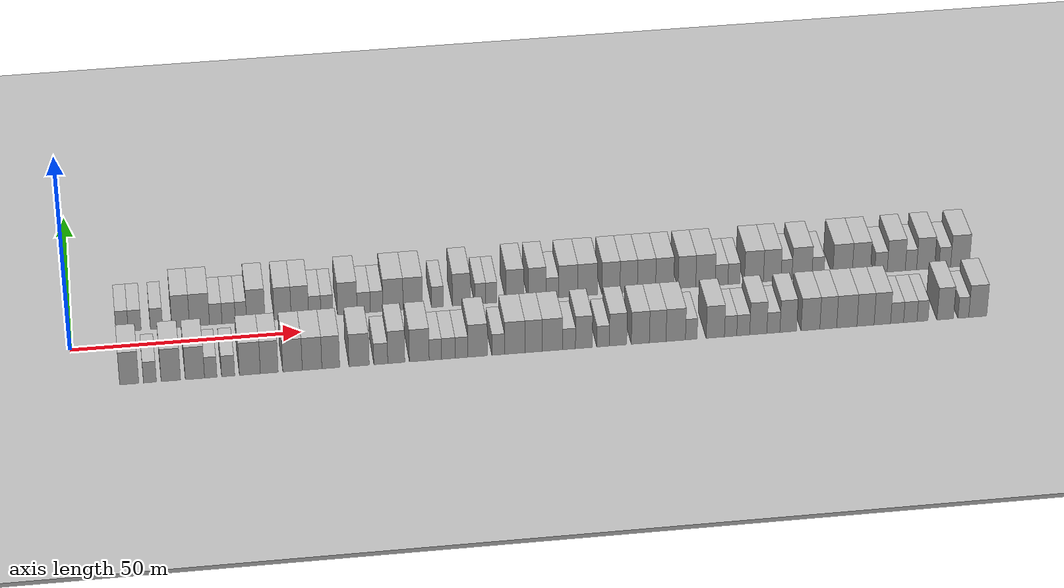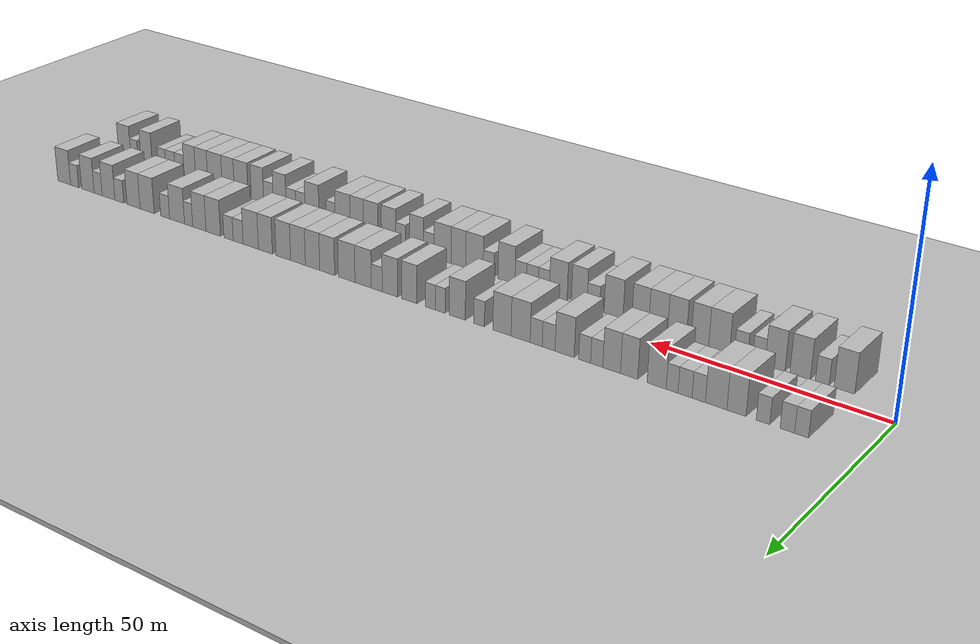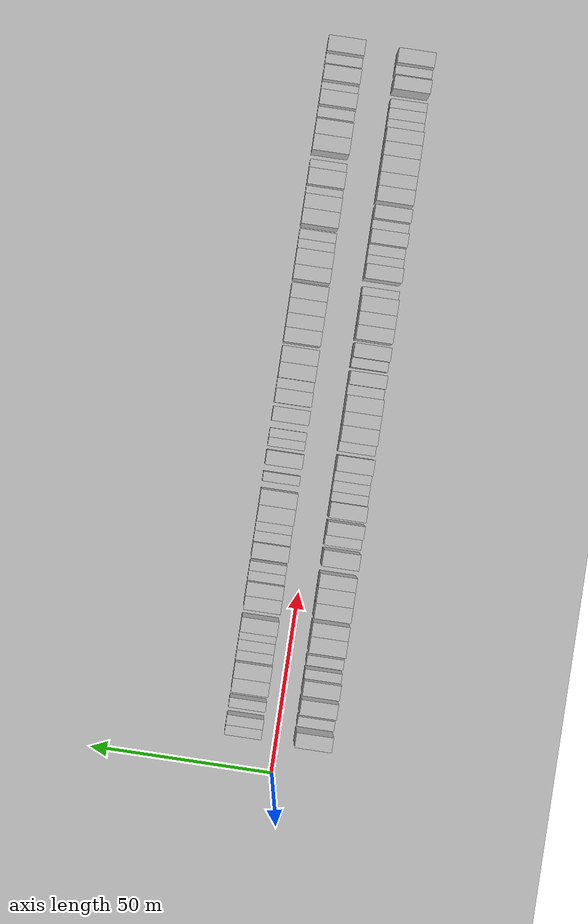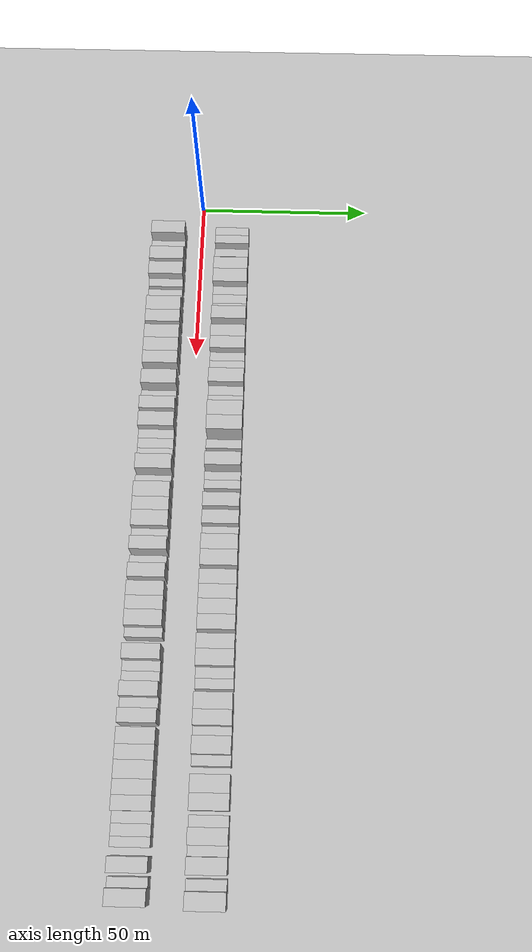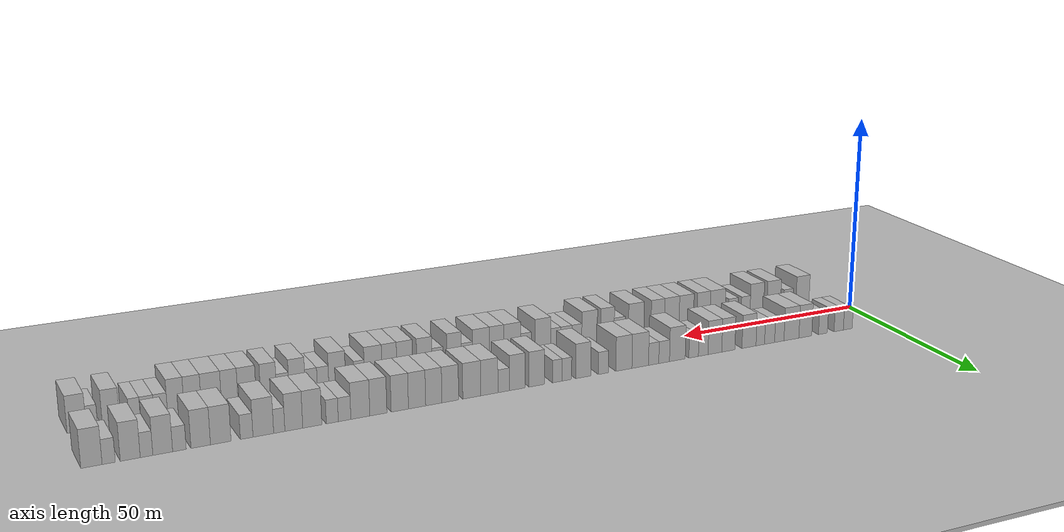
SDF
<?xml version="1.0" encoding="utf-8"?>

<sdf version="1.6">

   <world name="default">

      <gui fullscreen="0">

         <camera name="user_camera">

            <pose>-15 0 4.57585 0 0 0</pose>

            <view_controller>orbit</view_controller>

         </camera>

      </gui>

      <scene>

         <sky>

           <clouds>

             <speed>12</speed>

           </clouds>

         </sky>

         <ambient>0.4 0.4 0.4 1</ambient>

         <background>0.7 0.7 0.7 1</background>

         <shadows>1</shadows>

      </scene>

      <gravity>0 0 -9.8066</gravity>

      <magnetic_field>6e-06 2.3e-05 -4.2e-05</magnetic_field>

      <physics default="0" name="default_physics" type="ode">

         <ode>

            <solver>

               <type>quick</type>

               <iters>10</iters>

               <sor>1.0</sor>

               <use_dynamic_moi_rescaling>0</use_dynamic_moi_rescaling>

            </solver>

            <constraints>

               <cfm>0</cfm>

               <erp>0.2</erp>

               <contact_max_correcting_vel>100</contact_max_correcting_vel>

               <contact_surface_layer>0.001</contact_surface_layer>

            </constraints>

         </ode>

         <max_step_size>0.004</max_step_size>

         <real_time_factor>1</real_time_factor>

         <real_time_update_rate>250</real_time_update_rate>

      </physics>

      <light name="sun" type="directional">

         <cast_shadows>1</cast_shadows>

         <pose>0 0 10 0 0 0</pose>

         <diffuse>0.8 0.8 0.8 1</diffuse>

         <specular>0.2 0.2 0.2 1</specular>

         <attenuation>

            <range>1000</range>

            <constant>0.9</constant>

            <linear>0.01</linear>

            <quadratic>0.001</quadratic>

         </attenuation>

         <direction>-0.5 0.1 -0.9</direction>

      </light>

      <include>

         <name>ground_plane_1</name>

         <uri>model://HANNAS_ground_plane</uri>

         <pose>0 0 0  0 0 0</pose>

      </include>

      <include>

         <name>ground_plane_2</name>

         <uri>model://HANNAS_ground_plane</uri>

         <pose>100 0 0  0 0 0</pose>

      </include>

      <model name="building_1">

         <static>1</static>

         <pose frame="">11.3415 9.5000 0 0.000000 0.000000 1.570796</pose>

         <link name="link">

            <pose frame="">0 0 3.00 0 0 0</pose>

            <collision name="collision">

               <geometry>

                  <box>

                     <size>10.0000 2.6829 6.0000</size>

                  </box>

               </geometry>

               <max_contacts>10</max_contacts>

               <surface>

                  <contact>

                     <ode/>

                  </contact>

                  <bounce/>

                  <friction>

                     <torsional>

                        <ode/>

                     </torsional>

                     <ode/>

                  </friction>

               </surface>

            </collision>

            <visual name="visual">

               <cast_shadows>0</cast_shadows>

               <geometry>

                  <box>

                     <size>10.0000 2.6829 6.0000</size>

                  </box>

               </geometry>

               <material>

                  <script>

                     <uri>model://HANNAS_wall/materials/scripts</uri>

                     <uri>model://HANNAS_wall/materials/textures</uri>

                     <name>vrc/HANNAS_wall</name>

                  </script>

               </material>

            </visual>

            <self_collide>0</self_collide>

            <enable_wind>0</enable_wind>

            <kinematic>0</kinematic>

         </link>

      </model>

      <model name="building_2">

         <static>1</static>

         <pose frame="">14.0803 9.5000 0 0.000000 0.000000 1.570796</pose>

         <link name="link">

            <pose frame="">0 0 3.00 0 0 0</pose>

            <collision name="collision">

               <geometry>

                  <box>

                     <size>10.0000 2.7948 6.0000</size>

                  </box>

               </geometry>

               <max_contacts>10</max_contacts>

               <surface>

                  <contact>

                     <ode/>

                  </contact>

                  <bounce/>

                  <friction>

                     <torsional>

                        <ode/>

                     </torsional>

                     <ode/>

                  </friction>

               </surface>

            </collision>

            <visual name="visual">

               <cast_shadows>0</cast_shadows>

               <geometry>

                  <box>

                     <size>10.0000 2.7948 6.0000</size>

                  </box>

               </geometry>

               <material>

                  <script>

                     <uri>model://HANNAS_wall/materials/scripts</uri>

                     <uri>model://HANNAS_wall/materials/textures</uri>

                     <name>vrc/HANNAS_wall</name>

                  </script>

               </material>

            </visual>

            <self_collide>0</self_collide>

            <enable_wind>0</enable_wind>

            <kinematic>0</kinematic>

         </link>

      </model>

      <model name="building_3">

         <static>1</static>

         <pose frame="">18.8091 9.5000 0 0.000000 0.000000 1.570796</pose>

         <link name="link">

            <pose frame="">0 0 3.00 0 0 0</pose>

            <collision name="collision">

               <geometry>

                  <box>

                     <size>10.0000 2.6627 6.0000</size>

                  </box>

               </geometry>

               <max_contacts>10</max_contacts>

               <surface>

                  <contact>

                     <ode/>

                  </contact>

                  <bounce/>

                  <friction>

                     <torsional>

                        <ode/>

                     </torsional>

                     <ode/>

                  </friction>

               </surface>

            </collision>

            <visual name="visual">

               <cast_shadows>0</cast_shadows>

               <geometry>

                  <box>

                     <size>10.0000 2.6627 6.0000</size>

                  </box>

               </geometry>

               <material>

                  <script>

                     <uri>model://HANNAS_wall/materials/scripts</uri>

                     <uri>model://HANNAS_wall/materials/textures</uri>

                     <name>vrc/HANNAS_wall</name>

                  </script>

               </material>

            </visual>

            <self_collide>0</self_collide>

            <enable_wind>0</enable_wind>

            <kinematic>0</kinematic>

         </link>

      </model>

      <model name="building_4">

         <static>1</static>

         <pose frame="">24.0546 9.5000 0 0.000000 0.000000 1.570796</pose>

         <link name="link">

            <pose frame="">0 0 4.50 0 0 0</pose>

            <collision name="collision">

               <geometry>

                  <box>

                     <size>10.0000 3.8284 9.0000</size>

                  </box>

               </geometry>

               <max_contacts>10</max_contacts>

               <surface>

                  <contact>

                     <ode/>

                  </contact>

                  <bounce/>

                  <friction>

                     <torsional>

                        <ode/>

                     </torsional>

                     <ode/>

                  </friction>

               </surface>

            </collision>

            <visual name="visual">

               <cast_shadows>0</cast_shadows>

               <geometry>

                  <box>

                     <size>10.0000 3.8284 9.0000</size>

                  </box>

               </geometry>

               <material>

                  <script>

                     <uri>model://HANNAS_wall/materials/scripts</uri>

                     <uri>model://HANNAS_wall/materials/textures</uri>

                     <name>vrc/HANNAS_wall</name>

                  </script>

               </material>

            </visual>

            <self_collide>0</self_collide>

            <enable_wind>0</enable_wind>

            <kinematic>0</kinematic>

         </link>

      </model>

      <model name="building_5">

         <static>1</static>

         <pose frame="">28.1454 9.5000 0 0.000000 0.000000 1.570796</pose>

         <link name="link">

            <pose frame="">0 0 4.50 0 0 0</pose>

            <collision name="collision">

               <geometry>

                  <box>

                     <size>10.0000 4.3533 9.0000</size>

                  </box>

               </geometry>

               <max_contacts>10</max_contacts>

               <surface>

                  <contact>

                     <ode/>

                  </contact>

                  <bounce/>

                  <friction>

                     <torsional>

                        <ode/>

                     </torsional>

                     <ode/>

                  </friction>

               </surface>

            </collision>

            <visual name="visual">

               <cast_shadows>0</cast_shadows>

               <geometry>

                  <box>

                     <size>10.0000 4.3533 9.0000</size>

                  </box>

               </geometry>

               <material>

                  <script>

                     <uri>model://HANNAS_wall/materials/scripts</uri>

                     <uri>model://HANNAS_wall/materials/textures</uri>

                     <name>vrc/HANNAS_wall</name>

                  </script>

               </material>

            </visual>

            <self_collide>0</self_collide>

            <enable_wind>0</enable_wind>

            <kinematic>0</kinematic>

         </link>

      </model>

      <model name="building_6">

         <static>1</static>

         <pose frame="">31.6854 9.5000 0 0.000000 0.000000 1.570796</pose>

         <link name="link">

            <pose frame="">0 0 3.00 0 0 0</pose>

            <collision name="collision">

               <geometry>

                  <box>

                     <size>10.0000 2.7267 6.0000</size>

                  </box>

               </geometry>

               <max_contacts>10</max_contacts>

               <surface>

                  <contact>

                     <ode/>

                  </contact>

                  <bounce/>

                  <friction>

                     <torsional>

                        <ode/>

                     </torsional>

                     <ode/>

                  </friction>

               </surface>

            </collision>

            <visual name="visual">

               <cast_shadows>0</cast_shadows>

               <geometry>

                  <box>

                     <size>10.0000 2.7267 6.0000</size>

                  </box>

               </geometry>

               <material>

                  <script>

                     <uri>model://HANNAS_wall/materials/scripts</uri>

                     <uri>model://HANNAS_wall/materials/textures</uri>

                     <name>vrc/HANNAS_wall</name>

                  </script>

               </material>

            </visual>

            <self_collide>0</self_collide>

            <enable_wind>0</enable_wind>

            <kinematic>0</kinematic>

         </link>

      </model>

      <model name="building_7">

         <static>1</static>

         <pose frame="">34.5057 9.5000 0 0.000000 0.000000 1.570796</pose>

         <link name="link">

            <pose frame="">0 0 3.00 0 0 0</pose>

            <collision name="collision">

               <geometry>

                  <box>

                     <size>10.0000 2.9138 6.0000</size>

                  </box>

               </geometry>

               <max_contacts>10</max_contacts>

               <surface>

                  <contact>

                     <ode/>

                  </contact>

                  <bounce/>

                  <friction>

                     <torsional>

                        <ode/>

                     </torsional>

                     <ode/>

                  </friction>

               </surface>

            </collision>

            <visual name="visual">

               <cast_shadows>0</cast_shadows>

               <geometry>

                  <box>

                     <size>10.0000 2.9138 6.0000</size>

                  </box>

               </geometry>

               <material>

                  <script>

                     <uri>model://HANNAS_wall/materials/scripts</uri>

                     <uri>model://HANNAS_wall/materials/textures</uri>

                     <name>vrc/HANNAS_wall</name>

                  </script>

               </material>

            </visual>

            <self_collide>0</self_collide>

            <enable_wind>0</enable_wind>

            <kinematic>0</kinematic>

         </link>

      </model>

      <model name="building_8">

         <static>1</static>

         <pose frame="">37.1857 9.5000 0 0.000000 0.000000 1.570796</pose>

         <link name="link">

            <pose frame="">0 0 3.00 0 0 0</pose>

            <collision name="collision">

               <geometry>

                  <box>

                     <size>10.0000 2.4462 6.0000</size>

                  </box>

               </geometry>

               <max_contacts>10</max_contacts>

               <surface>

                  <contact>

                     <ode/>

                  </contact>

                  <bounce/>

                  <friction>

                     <torsional>

                        <ode/>

                     </torsional>

                     <ode/>

                  </friction>

               </surface>

            </collision>

            <visual name="visual">

               <cast_shadows>0</cast_shadows>

               <geometry>

                  <box>

                     <size>10.0000 2.4462 6.0000</size>

                  </box>

               </geometry>

               <material>

                  <script>

                     <uri>model://HANNAS_wall/materials/scripts</uri>

                     <uri>model://HANNAS_wall/materials/textures</uri>

                     <name>vrc/HANNAS_wall</name>

                  </script>

               </material>

            </visual>

            <self_collide>0</self_collide>

            <enable_wind>0</enable_wind>

            <kinematic>0</kinematic>

         </link>

      </model>

      <model name="building_9">

         <static>1</static>

         <pose frame="">40.4200 9.5000 0 0.000000 0.000000 1.570796</pose>

         <link name="link">

            <pose frame="">0 0 4.50 0 0 0</pose>

            <collision name="collision">

               <geometry>

                  <box>

                     <size>10.0000 4.0225 9.0000</size>

                  </box>

               </geometry>

               <max_contacts>10</max_contacts>

               <surface>

                  <contact>

                     <ode/>

                  </contact>

                  <bounce/>

                  <friction>

                     <torsional>

                        <ode/>

                     </torsional>

                     <ode/>

                  </friction>

               </surface>

            </collision>

            <visual name="visual">

               <cast_shadows>0</cast_shadows>

               <geometry>

                  <box>

                     <size>10.0000 4.0225 9.0000</size>

                  </box>

               </geometry>

               <material>

                  <script>

                     <uri>model://HANNAS_wall/materials/scripts</uri>

                     <uri>model://HANNAS_wall/materials/textures</uri>

                     <name>vrc/HANNAS_wall</name>

                  </script>

               </material>

            </visual>

            <self_collide>0</self_collide>

            <enable_wind>0</enable_wind>

            <kinematic>0</kinematic>

         </link>

      </model>

      <model name="building_10">

         <static>1</static>

         <pose frame="">46.2877 9.5000 0 0.000000 0.000000 1.570796</pose>

         <link name="link">

            <pose frame="">0 0 4.50 0 0 0</pose>

            <collision name="collision">

               <geometry>

                  <box>

                     <size>10.0000 3.7129 9.0000</size>

                  </box>

               </geometry>

               <max_contacts>10</max_contacts>

               <surface>

                  <contact>

                     <ode/>

                  </contact>

                  <bounce/>

                  <friction>

                     <torsional>

                        <ode/>

                     </torsional>

                     <ode/>

                  </friction>

               </surface>

            </collision>

            <visual name="visual">

               <cast_shadows>0</cast_shadows>

               <geometry>

                  <box>

                     <size>10.0000 3.7129 9.0000</size>

                  </box>

               </geometry>

               <material>

                  <script>

                     <uri>model://HANNAS_wall/materials/scripts</uri>

                     <uri>model://HANNAS_wall/materials/textures</uri>

                     <name>vrc/HANNAS_wall</name>

                  </script>

               </material>

            </visual>

            <self_collide>0</self_collide>

            <enable_wind>0</enable_wind>

            <kinematic>0</kinematic>

         </link>

      </model>

      <model name="building_11">

         <static>1</static>

         <pose frame="">50.0635 9.5000 0 0.000000 0.000000 1.570796</pose>

         <link name="link">

            <pose frame="">0 0 4.50 0 0 0</pose>

            <collision name="collision">

               <geometry>

                  <box>

                     <size>10.0000 3.8388 9.0000</size>

                  </box>

               </geometry>

               <max_contacts>10</max_contacts>

               <surface>

                  <contact>

                     <ode/>

                  </contact>

                  <bounce/>

                  <friction>

                     <torsional>

                        <ode/>

                     </torsional>

                     <ode/>

                  </friction>

               </surface>

            </collision>

            <visual name="visual">

               <cast_shadows>0</cast_shadows>

               <geometry>

                  <box>

                     <size>10.0000 3.8388 9.0000</size>

                  </box>

               </geometry>

               <material>

                  <script>

                     <uri>model://HANNAS_wall/materials/scripts</uri>

                     <uri>model://HANNAS_wall/materials/textures</uri>

                     <name>vrc/HANNAS_wall</name>

                  </script>

               </material>

            </visual>

            <self_collide>0</self_collide>

            <enable_wind>0</enable_wind>

            <kinematic>0</kinematic>

         </link>

      </model>

      <model name="building_12">

         <static>1</static>

         <pose frame="">53.3202 9.5000 0 0.000000 0.000000 1.570796</pose>

         <link name="link">

            <pose frame="">0 0 3.00 0 0 0</pose>

            <collision name="collision">

               <geometry>

                  <box>

                     <size>10.0000 2.6747 6.0000</size>

                  </box>

               </geometry>

               <max_contacts>10</max_contacts>

               <surface>

                  <contact>

                     <ode/>

                  </contact>

                  <bounce/>

                  <friction>

                     <torsional>

                        <ode/>

                     </torsional>

                     <ode/>

                  </friction>

               </surface>

            </collision>

            <visual name="visual">

               <cast_shadows>0</cast_shadows>

               <geometry>

                  <box>

                     <size>10.0000 2.6747 6.0000</size>

                  </box>

               </geometry>

               <material>

                  <script>

                     <uri>model://HANNAS_wall/materials/scripts</uri>

                     <uri>model://HANNAS_wall/materials/textures</uri>

                     <name>vrc/HANNAS_wall</name>

                  </script>

               </material>

            </visual>

            <self_collide>0</self_collide>

            <enable_wind>0</enable_wind>

            <kinematic>0</kinematic>

         </link>

      </model>

      <model name="building_13">

         <static>1</static>

         <pose frame="">55.9779 9.5000 0 0.000000 0.000000 1.570796</pose>

         <link name="link">

            <pose frame="">0 0 3.00 0 0 0</pose>

            <collision name="collision">

               <geometry>

                  <box>

                     <size>10.0000 2.6407 6.0000</size>

                  </box>

               </geometry>

               <max_contacts>10</max_contacts>

               <surface>

                  <contact>

                     <ode/>

                  </contact>

                  <bounce/>

                  <friction>

                     <torsional>

                        <ode/>

                     </torsional>

                     <ode/>

                  </friction>

               </surface>

            </collision>

            <visual name="visual">

               <cast_shadows>0</cast_shadows>

               <geometry>

                  <box>

                     <size>10.0000 2.6407 6.0000</size>

                  </box>

               </geometry>

               <material>

                  <script>

                     <uri>model://HANNAS_wall/materials/scripts</uri>

                     <uri>model://HANNAS_wall/materials/textures</uri>

                     <name>vrc/HANNAS_wall</name>

                  </script>

               </material>

            </visual>

            <self_collide>0</self_collide>

            <enable_wind>0</enable_wind>

            <kinematic>0</kinematic>

         </link>

      </model>

      <model name="building_14">

         <static>1</static>

         <pose frame="">60.4485 9.5000 0 0.000000 0.000000 1.570796</pose>

         <link name="link">

            <pose frame="">0 0 4.50 0 0 0</pose>

            <collision name="collision">

               <geometry>

                  <box>

                     <size>10.0000 4.3005 9.0000</size>

                  </box>

               </geometry>

               <max_contacts>10</max_contacts>

               <surface>

                  <contact>

                     <ode/>

                  </contact>

                  <bounce/>

                  <friction>

                     <torsional>

                        <ode/>

                     </torsional>

                     <ode/>

                  </friction>

               </surface>

            </collision>

            <visual name="visual">

               <cast_shadows>0</cast_shadows>

               <geometry>

                  <box>

                     <size>10.0000 4.3005 9.0000</size>

                  </box>

               </geometry>

               <material>

                  <script>

                     <uri>model://HANNAS_wall/materials/scripts</uri>

                     <uri>model://HANNAS_wall/materials/textures</uri>

                     <name>vrc/HANNAS_wall</name>

                  </script>

               </material>

            </visual>

            <self_collide>0</self_collide>

            <enable_wind>0</enable_wind>

            <kinematic>0</kinematic>

         </link>

      </model>

      <model name="building_15">

         <static>1</static>

         <pose frame="">64.0582 9.5000 0 0.000000 0.000000 1.570796</pose>

         <link name="link">

            <pose frame="">0 0 3.00 0 0 0</pose>

            <collision name="collision">

               <geometry>

                  <box>

                     <size>10.0000 2.9188 6.0000</size>

                  </box>

               </geometry>

               <max_contacts>10</max_contacts>

               <surface>

                  <contact>

                     <ode/>

                  </contact>

                  <bounce/>

                  <friction>

                     <torsional>

                        <ode/>

                     </torsional>

                     <ode/>

                  </friction>

               </surface>

            </collision>

            <visual name="visual">

               <cast_shadows>0</cast_shadows>

               <geometry>

                  <box>

                     <size>10.0000 2.9188 6.0000</size>

                  </box>

               </geometry>

               <material>

                  <script>

                     <uri>model://HANNAS_wall/materials/scripts</uri>

                     <uri>model://HANNAS_wall/materials/textures</uri>

                     <name>vrc/HANNAS_wall</name>

                  </script>

               </material>

            </visual>

            <self_collide>0</self_collide>

            <enable_wind>0</enable_wind>

            <kinematic>0</kinematic>

         </link>

      </model>

      <model name="building_16">

         <static>1</static>

         <pose frame="">66.8969 9.5000 0 0.000000 0.000000 1.570796</pose>

         <link name="link">

            <pose frame="">0 0 3.00 0 0 0</pose>

            <collision name="collision">

               <geometry>

                  <box>

                     <size>10.0000 2.7586 6.0000</size>

                  </box>

               </geometry>

               <max_contacts>10</max_contacts>

               <surface>

                  <contact>

                     <ode/>

                  </contact>

                  <bounce/>

                  <friction>

                     <torsional>

                        <ode/>

                     </torsional>

                     <ode/>

                  </friction>

               </surface>

            </collision>

            <visual name="visual">

               <cast_shadows>0</cast_shadows>

               <geometry>

                  <box>

                     <size>10.0000 2.7586 6.0000</size>

                  </box>

               </geometry>

               <material>

                  <script>

                     <uri>model://HANNAS_wall/materials/scripts</uri>

                     <uri>model://HANNAS_wall/materials/textures</uri>

                     <name>vrc/HANNAS_wall</name>

                  </script>

               </material>

            </visual>

            <self_collide>0</self_collide>

            <enable_wind>0</enable_wind>

            <kinematic>0</kinematic>

         </link>

      </model>

      <model name="building_17">

         <static>1</static>

         <pose frame="">70.4968 9.5000 0 0.000000 0.000000 1.570796</pose>

         <link name="link">

            <pose frame="">0 0 4.50 0 0 0</pose>

            <collision name="collision">

               <geometry>

                  <box>

                     <size>10.0000 4.4412 9.0000</size>

                  </box>

               </geometry>

               <max_contacts>10</max_contacts>

               <surface>

                  <contact>

                     <ode/>

                  </contact>

                  <bounce/>

                  <friction>

                     <torsional>

                        <ode/>

                     </torsional>

                     <ode/>

                  </friction>

               </surface>

            </collision>

            <visual name="visual">

               <cast_shadows>0</cast_shadows>

               <geometry>

                  <box>

                     <size>10.0000 4.4412 9.0000</size>

                  </box>

               </geometry>

               <material>

                  <script>

                     <uri>model://HANNAS_wall/materials/scripts</uri>

                     <uri>model://HANNAS_wall/materials/textures</uri>

                     <name>vrc/HANNAS_wall</name>

                  </script>

               </material>

            </visual>

            <self_collide>0</self_collide>

            <enable_wind>0</enable_wind>

            <kinematic>0</kinematic>

         </link>

      </model>

      <model name="building_18">

         <static>1</static>

         <pose frame="">74.8519 9.5000 0 0.000000 0.000000 1.570796</pose>

         <link name="link">

            <pose frame="">0 0 4.50 0 0 0</pose>

            <collision name="collision">

               <geometry>

                  <box>

                     <size>10.0000 4.2689 9.0000</size>

                  </box>

               </geometry>

               <max_contacts>10</max_contacts>

               <surface>

                  <contact>

                     <ode/>

                  </contact>

                  <bounce/>

                  <friction>

                     <torsional>

                        <ode/>

                     </torsional>

                     <ode/>

                  </friction>

               </surface>

            </collision>

            <visual name="visual">

               <cast_shadows>0</cast_shadows>

               <geometry>

                  <box>

                     <size>10.0000 4.2689 9.0000</size>

                  </box>

               </geometry>

               <material>

                  <script>

                     <uri>model://HANNAS_wall/materials/scripts</uri>

                     <uri>model://HANNAS_wall/materials/textures</uri>

                     <name>vrc/HANNAS_wall</name>

                  </script>

               </material>

            </visual>

            <self_collide>0</self_collide>

            <enable_wind>0</enable_wind>

            <kinematic>0</kinematic>

         </link>

      </model>

      <model name="building_19">

         <static>1</static>

         <pose frame="">80.2871 9.5000 0 0.000000 0.000000 1.570796</pose>

         <link name="link">

            <pose frame="">0 0 3.00 0 0 0</pose>

            <collision name="collision">

               <geometry>

                  <box>

                     <size>10.0000 2.6015 6.0000</size>

                  </box>

               </geometry>

               <max_contacts>10</max_contacts>

               <surface>

                  <contact>

                     <ode/>

                  </contact>

                  <bounce/>

                  <friction>

                     <torsional>

                        <ode/>

                     </torsional>

                     <ode/>

                  </friction>

               </surface>

            </collision>

            <visual name="visual">

               <cast_shadows>0</cast_shadows>

               <geometry>

                  <box>

                     <size>10.0000 2.6015 6.0000</size>

                  </box>

               </geometry>

               <material>

                  <script>

                     <uri>model://HANNAS_wall/materials/scripts</uri>

                     <uri>model://HANNAS_wall/materials/textures</uri>

                     <name>vrc/HANNAS_wall</name>

                  </script>

               </material>

            </visual>

            <self_collide>0</self_collide>

            <enable_wind>0</enable_wind>

            <kinematic>0</kinematic>

         </link>

      </model>

      <model name="building_20">

         <static>1</static>

         <pose frame="">85.5526 9.5000 0 0.000000 0.000000 1.570796</pose>

         <link name="link">

            <pose frame="">0 0 4.50 0 0 0</pose>

            <collision name="collision">

               <geometry>

                  <box>

                     <size>10.0000 3.9295 9.0000</size>

                  </box>

               </geometry>

               <max_contacts>10</max_contacts>

               <surface>

                  <contact>

                     <ode/>

                  </contact>

                  <bounce/>

                  <friction>

                     <torsional>

                        <ode/>

                     </torsional>

                     <ode/>

                  </friction>

               </surface>

            </collision>

            <visual name="visual">

               <cast_shadows>0</cast_shadows>

               <geometry>

                  <box>

                     <size>10.0000 3.9295 9.0000</size>

                  </box>

               </geometry>

               <material>

                  <script>

                     <uri>model://HANNAS_wall/materials/scripts</uri>

                     <uri>model://HANNAS_wall/materials/textures</uri>

                     <name>vrc/HANNAS_wall</name>

                  </script>

               </material>

            </visual>

            <self_collide>0</self_collide>

            <enable_wind>0</enable_wind>

            <kinematic>0</kinematic>

         </link>

      </model>

      <model name="building_21">

         <static>1</static>

         <pose frame="">89.7379 9.5000 0 0.000000 0.000000 1.570796</pose>

         <link name="link">

            <pose frame="">0 0 3.00 0 0 0</pose>

            <collision name="collision">

               <geometry>

                  <box>

                     <size>10.0000 2.4410 6.0000</size>

                  </box>

               </geometry>

               <max_contacts>10</max_contacts>

               <surface>

                  <contact>

                     <ode/>

                  </contact>

                  <bounce/>

                  <friction>

                     <torsional>

                        <ode/>

                     </torsional>

                     <ode/>

                  </friction>

               </surface>

            </collision>

            <visual name="visual">

               <cast_shadows>0</cast_shadows>

               <geometry>

                  <box>

                     <size>10.0000 2.4410 6.0000</size>

                  </box>

               </geometry>

               <material>

                  <script>

                     <uri>model://HANNAS_wall/materials/scripts</uri>

                     <uri>model://HANNAS_wall/materials/textures</uri>

                     <name>vrc/HANNAS_wall</name>

                  </script>

               </material>

            </visual>

            <self_collide>0</self_collide>

            <enable_wind>0</enable_wind>

            <kinematic>0</kinematic>

         </link>

      </model>

      <model name="building_22">

         <static>1</static>

         <pose frame="">92.1954 9.5000 0 0.000000 0.000000 1.570796</pose>

         <link name="link">

            <pose frame="">0 0 3.00 0 0 0</pose>

            <collision name="collision">

               <geometry>

                  <box>

                     <size>10.0000 2.4740 6.0000</size>

                  </box>

               </geometry>

               <max_contacts>10</max_contacts>

               <surface>

                  <contact>

                     <ode/>

                  </contact>

                  <bounce/>

                  <friction>

                     <torsional>

                        <ode/>

                     </torsional>

                     <ode/>

                  </friction>

               </surface>

            </collision>

            <visual name="visual">

               <cast_shadows>0</cast_shadows>

               <geometry>

                  <box>

                     <size>10.0000 2.4740 6.0000</size>

                  </box>

               </geometry>

               <material>

                  <script>

                     <uri>model://HANNAS_wall/materials/scripts</uri>

                     <uri>model://HANNAS_wall/materials/textures</uri>

                     <name>vrc/HANNAS_wall</name>

                  </script>

               </material>

            </visual>

            <self_collide>0</self_collide>

            <enable_wind>0</enable_wind>

            <kinematic>0</kinematic>

         </link>

      </model>

      <model name="building_23">

         <static>1</static>

         <pose frame="">97.3916 9.5000 0 0.000000 0.000000 1.570796</pose>

         <link name="link">

            <pose frame="">0 0 4.50 0 0 0</pose>

            <collision name="collision">

               <geometry>

                  <box>

                     <size>10.0000 3.9183 9.0000</size>

                  </box>

               </geometry>

               <max_contacts>10</max_contacts>

               <surface>

                  <contact>

                     <ode/>

                  </contact>

                  <bounce/>

                  <friction>

                     <torsional>

                        <ode/>

                     </torsional>

                     <ode/>

                  </friction>

               </surface>

            </collision>

            <visual name="visual">

               <cast_shadows>0</cast_shadows>

               <geometry>

                  <box>

                     <size>10.0000 3.9183 9.0000</size>

                  </box>

               </geometry>

               <material>

                  <script>

                     <uri>model://HANNAS_wall/materials/scripts</uri>

                     <uri>model://HANNAS_wall/materials/textures</uri>

                     <name>vrc/HANNAS_wall</name>

                  </script>

               </material>

            </visual>

            <self_collide>0</self_collide>

            <enable_wind>0</enable_wind>

            <kinematic>0</kinematic>

         </link>

      </model>

      <model name="building_24">

         <static>1</static>

         <pose frame="">102.3076 9.5000 0 0.000000 0.000000 1.570796</pose>

         <link name="link">

            <pose frame="">0 0 4.50 0 0 0</pose>

            <collision name="collision">

               <geometry>

                  <box>

                     <size>10.0000 3.9137 9.0000</size>

                  </box>

               </geometry>

               <max_contacts>10</max_contacts>

               <surface>

                  <contact>

                     <ode/>

                  </contact>

                  <bounce/>

                  <friction>

                     <torsional>

                        <ode/>

                     </torsional>

                     <ode/>

                  </friction>

               </surface>

            </collision>

            <visual name="visual">

               <cast_shadows>0</cast_shadows>

               <geometry>

                  <box>

                     <size>10.0000 3.9137 9.0000</size>

                  </box>

               </geometry>

               <material>

                  <script>

                     <uri>model://HANNAS_wall/materials/scripts</uri>

                     <uri>model://HANNAS_wall/materials/textures</uri>

                     <name>vrc/HANNAS_wall</name>

                  </script>

               </material>

            </visual>

            <self_collide>0</self_collide>

            <enable_wind>0</enable_wind>

            <kinematic>0</kinematic>

         </link>

      </model>

      <model name="building_25">

         <static>1</static>

         <pose frame="">105.6866 9.5000 0 0.000000 0.000000 1.570796</pose>

         <link name="link">

            <pose frame="">0 0 3.00 0 0 0</pose>

            <collision name="collision">

               <geometry>

                  <box>

                     <size>10.0000 2.8443 6.0000</size>

                  </box>

               </geometry>

               <max_contacts>10</max_contacts>

               <surface>

                  <contact>

                     <ode/>

                  </contact>

                  <bounce/>

                  <friction>

                     <torsional>

                        <ode/>

                     </torsional>

                     <ode/>

                  </friction>

               </surface>

            </collision>

            <visual name="visual">

               <cast_shadows>0</cast_shadows>

               <geometry>

                  <box>

                     <size>10.0000 2.8443 6.0000</size>

                  </box>

               </geometry>

               <material>

                  <script>

                     <uri>model://HANNAS_wall/materials/scripts</uri>

                     <uri>model://HANNAS_wall/materials/textures</uri>

                     <name>vrc/HANNAS_wall</name>

                  </script>

               </material>

            </visual>

            <self_collide>0</self_collide>

            <enable_wind>0</enable_wind>

            <kinematic>0</kinematic>

         </link>

      </model>

      <model name="building_26">

         <static>1</static>

         <pose frame="">109.2234 9.5000 0 0.000000 0.000000 1.570796</pose>

         <link name="link">

            <pose frame="">0 0 4.50 0 0 0</pose>

            <collision name="collision">

               <geometry>

                  <box>

                     <size>10.0000 4.2293 9.0000</size>

                  </box>

               </geometry>

               <max_contacts>10</max_contacts>

               <surface>

                  <contact>

                     <ode/>

                  </contact>

                  <bounce/>

                  <friction>

                     <torsional>

                        <ode/>

                     </torsional>

                     <ode/>

                  </friction>

               </surface>

            </collision>

            <visual name="visual">

               <cast_shadows>0</cast_shadows>

               <geometry>

                  <box>

                     <size>10.0000 4.2293 9.0000</size>

                  </box>

               </geometry>

               <material>

                  <script>

                     <uri>model://HANNAS_wall/materials/scripts</uri>

                     <uri>model://HANNAS_wall/materials/textures</uri>

                     <name>vrc/HANNAS_wall</name>

                  </script>

               </material>

            </visual>

            <self_collide>0</self_collide>

            <enable_wind>0</enable_wind>

            <kinematic>0</kinematic>

         </link>

      </model>

      <model name="building_27">

         <static>1</static>

         <pose frame="">113.5331 9.5000 0 0.000000 0.000000 1.570796</pose>

         <link name="link">

            <pose frame="">0 0 4.50 0 0 0</pose>

            <collision name="collision">

               <geometry>

                  <box>

                     <size>10.0000 4.3900 9.0000</size>

                  </box>

               </geometry>

               <max_contacts>10</max_contacts>

               <surface>

                  <contact>

                     <ode/>

                  </contact>

                  <bounce/>

                  <friction>

                     <torsional>

                        <ode/>

                     </torsional>

                     <ode/>

                  </friction>

               </surface>

            </collision>

            <visual name="visual">

               <cast_shadows>0</cast_shadows>

               <geometry>

                  <box>

                     <size>10.0000 4.3900 9.0000</size>

                  </box>

               </geometry>

               <material>

                  <script>

                     <uri>model://HANNAS_wall/materials/scripts</uri>

                     <uri>model://HANNAS_wall/materials/textures</uri>

                     <name>vrc/HANNAS_wall</name>

                  </script>

               </material>

            </visual>

            <self_collide>0</self_collide>

            <enable_wind>0</enable_wind>

            <kinematic>0</kinematic>

         </link>

      </model>

      <model name="building_28">

         <static>1</static>

         <pose frame="">118.7385 9.5000 0 0.000000 0.000000 1.570796</pose>

         <link name="link">

            <pose frame="">0 0 4.50 0 0 0</pose>

            <collision name="collision">

               <geometry>

                  <box>

                     <size>10.0000 4.0208 9.0000</size>

                  </box>

               </geometry>

               <max_contacts>10</max_contacts>

               <surface>

                  <contact>

                     <ode/>

                  </contact>

                  <bounce/>

                  <friction>

                     <torsional>

                        <ode/>

                     </torsional>

                     <ode/>

                  </friction>

               </surface>

            </collision>

            <visual name="visual">

               <cast_shadows>0</cast_shadows>

               <geometry>

                  <box>

                     <size>10.0000 4.0208 9.0000</size>

                  </box>

               </geometry>

               <material>

                  <script>

                     <uri>model://HANNAS_wall/materials/scripts</uri>

                     <uri>model://HANNAS_wall/materials/textures</uri>

                     <name>vrc/HANNAS_wall</name>

                  </script>

               </material>

            </visual>

            <self_collide>0</self_collide>

            <enable_wind>0</enable_wind>

            <kinematic>0</kinematic>

         </link>

      </model>

      <model name="building_29">

         <static>1</static>

         <pose frame="">122.6874 9.5000 0 0.000000 0.000000 1.570796</pose>

         <link name="link">

            <pose frame="">0 0 4.50 0 0 0</pose>

            <collision name="collision">

               <geometry>

                  <box>

                     <size>10.0000 3.8772 9.0000</size>

                  </box>

               </geometry>

               <max_contacts>10</max_contacts>

               <surface>

                  <contact>

                     <ode/>

                  </contact>

                  <bounce/>

                  <friction>

                     <torsional>

                        <ode/>

                     </torsional>

                     <ode/>

                  </friction>

               </surface>

            </collision>

            <visual name="visual">

               <cast_shadows>0</cast_shadows>

               <geometry>

                  <box>

                     <size>10.0000 3.8772 9.0000</size>

                  </box>

               </geometry>

               <material>

                  <script>

                     <uri>model://HANNAS_wall/materials/scripts</uri>

                     <uri>model://HANNAS_wall/materials/textures</uri>

                     <name>vrc/HANNAS_wall</name>

                  </script>

               </material>

            </visual>

            <self_collide>0</self_collide>

            <enable_wind>0</enable_wind>

            <kinematic>0</kinematic>

         </link>

      </model>

      <model name="building_30">

         <static>1</static>

         <pose frame="">126.6650 9.5000 0 0.000000 0.000000 1.570796</pose>

         <link name="link">

            <pose frame="">0 0 4.50 0 0 0</pose>

            <collision name="collision">

               <geometry>

                  <box>

                     <size>10.0000 4.0779 9.0000</size>

                  </box>

               </geometry>

               <max_contacts>10</max_contacts>

               <surface>

                  <contact>

                     <ode/>

                  </contact>

                  <bounce/>

                  <friction>

                     <torsional>

                        <ode/>

                     </torsional>

                     <ode/>

                  </friction>

               </surface>

            </collision>

            <visual name="visual">

               <cast_shadows>0</cast_shadows>

               <geometry>

                  <box>

                     <size>10.0000 4.0779 9.0000</size>

                  </box>

               </geometry>

               <material>

                  <script>

                     <uri>model://HANNAS_wall/materials/scripts</uri>

                     <uri>model://HANNAS_wall/materials/textures</uri>

                     <name>vrc/HANNAS_wall</name>

                  </script>

               </material>

            </visual>

            <self_collide>0</self_collide>

            <enable_wind>0</enable_wind>

            <kinematic>0</kinematic>

         </link>

      </model>

      <model name="building_31">

         <static>1</static>

         <pose frame="">130.7236 9.5000 0 0.000000 0.000000 1.570796</pose>

         <link name="link">

            <pose frame="">0 0 4.50 0 0 0</pose>

            <collision name="collision">

               <geometry>

                  <box>

                     <size>10.0000 4.0392 9.0000</size>

                  </box>

               </geometry>

               <max_contacts>10</max_contacts>

               <surface>

                  <contact>

                     <ode/>

                  </contact>

                  <bounce/>

                  <friction>

                     <torsional>

                        <ode/>

                     </torsional>

                     <ode/>

                  </friction>

               </surface>

            </collision>

            <visual name="visual">

               <cast_shadows>0</cast_shadows>

               <geometry>

                  <box>

                     <size>10.0000 4.0392 9.0000</size>

                  </box>

               </geometry>

               <material>

                  <script>

                     <uri>model://HANNAS_wall/materials/scripts</uri>

                     <uri>model://HANNAS_wall/materials/textures</uri>

                     <name>vrc/HANNAS_wall</name>

                  </script>

               </material>

            </visual>

            <self_collide>0</self_collide>

            <enable_wind>0</enable_wind>

            <kinematic>0</kinematic>

         </link>

      </model>

      <model name="building_32">

         <static>1</static>

         <pose frame="">135.7183 9.5000 0 0.000000 0.000000 1.570796</pose>

         <link name="link">

            <pose frame="">0 0 4.50 0 0 0</pose>

            <collision name="collision">

               <geometry>

                  <box>

                     <size>10.0000 3.9504 9.0000</size>

                  </box>

               </geometry>

               <max_contacts>10</max_contacts>

               <surface>

                  <contact>

                     <ode/>

                  </contact>

                  <bounce/>

                  <friction>

                     <torsional>

                        <ode/>

                     </torsional>

                     <ode/>

                  </friction>

               </surface>

            </collision>

            <visual name="visual">

               <cast_shadows>0</cast_shadows>

               <geometry>

                  <box>

                     <size>10.0000 3.9504 9.0000</size>

                  </box>

               </geometry>

               <material>

                  <script>

                     <uri>model://HANNAS_wall/materials/scripts</uri>

                     <uri>model://HANNAS_wall/materials/textures</uri>

                     <name>vrc/HANNAS_wall</name>

                  </script>

               </material>

            </visual>

            <self_collide>0</self_collide>

            <enable_wind>0</enable_wind>

            <kinematic>0</kinematic>

         </link>

      </model>

      <model name="building_33">

         <static>1</static>

         <pose frame="">139.8712 9.5000 0 0.000000 0.000000 1.570796</pose>

         <link name="link">

            <pose frame="">0 0 4.50 0 0 0</pose>

            <collision name="collision">

               <geometry>

                  <box>

                     <size>10.0000 4.3553 9.0000</size>

                  </box>

               </geometry>

               <max_contacts>10</max_contacts>

               <surface>

                  <contact>

                     <ode/>

                  </contact>

                  <bounce/>

                  <friction>

                     <torsional>

                        <ode/>

                     </torsional>

                     <ode/>

                  </friction>

               </surface>

            </collision>

            <visual name="visual">

               <cast_shadows>0</cast_shadows>

               <geometry>

                  <box>

                     <size>10.0000 4.3553 9.0000</size>

                  </box>

               </geometry>

               <material>

                  <script>

                     <uri>model://HANNAS_wall/materials/scripts</uri>

                     <uri>model://HANNAS_wall/materials/textures</uri>

                     <name>vrc/HANNAS_wall</name>

                  </script>

               </material>

            </visual>

            <self_collide>0</self_collide>

            <enable_wind>0</enable_wind>

            <kinematic>0</kinematic>

         </link>

      </model>

      <model name="building_34">

         <static>1</static>

         <pose frame="">143.4770 9.5000 0 0.000000 0.000000 1.570796</pose>

         <link name="link">

            <pose frame="">0 0 3.00 0 0 0</pose>

            <collision name="collision">

               <geometry>

                  <box>

                     <size>10.0000 2.8562 6.0000</size>

                  </box>

               </geometry>

               <max_contacts>10</max_contacts>

               <surface>

                  <contact>

                     <ode/>

                  </contact>

                  <bounce/>

                  <friction>

                     <torsional>

                        <ode/>

                     </torsional>

                     <ode/>

                  </friction>

               </surface>

            </collision>

            <visual name="visual">

               <cast_shadows>0</cast_shadows>

               <geometry>

                  <box>

                     <size>10.0000 2.8562 6.0000</size>

                  </box>

               </geometry>

               <material>

                  <script>

                     <uri>model://HANNAS_wall/materials/scripts</uri>

                     <uri>model://HANNAS_wall/materials/textures</uri>

                     <name>vrc/HANNAS_wall</name>

                  </script>

               </material>

            </visual>

            <self_collide>0</self_collide>

            <enable_wind>0</enable_wind>

            <kinematic>0</kinematic>

         </link>

      </model>

      <model name="building_35">

         <static>1</static>

         <pose frame="">146.2581 9.5000 0 0.000000 0.000000 1.570796</pose>

         <link name="link">

            <pose frame="">0 0 3.00 0 0 0</pose>

            <collision name="collision">

               <geometry>

                  <box>

                     <size>10.0000 2.7060 6.0000</size>

                  </box>

               </geometry>

               <max_contacts>10</max_contacts>

               <surface>

                  <contact>

                     <ode/>

                  </contact>

                  <bounce/>

                  <friction>

                     <torsional>

                        <ode/>

                     </torsional>

                     <ode/>

                  </friction>

               </surface>

            </collision>

            <visual name="visual">

               <cast_shadows>0</cast_shadows>

               <geometry>

                  <box>

                     <size>10.0000 2.7060 6.0000</size>

                  </box>

               </geometry>

               <material>

                  <script>

                     <uri>model://HANNAS_wall/materials/scripts</uri>

                     <uri>model://HANNAS_wall/materials/textures</uri>

                     <name>vrc/HANNAS_wall</name>

                  </script>

               </material>

            </visual>

            <self_collide>0</self_collide>

            <enable_wind>0</enable_wind>

            <kinematic>0</kinematic>

         </link>

      </model>

      <model name="building_36">

         <static>1</static>

         <pose frame="">150.7458 9.5000 0 0.000000 0.000000 1.570796</pose>

         <link name="link">

            <pose frame="">0 0 4.50 0 0 0</pose>

            <collision name="collision">

               <geometry>

                  <box>

                     <size>10.0000 4.2693 9.0000</size>

                  </box>

               </geometry>

               <max_contacts>10</max_contacts>

               <surface>

                  <contact>

                     <ode/>

                  </contact>

                  <bounce/>

                  <friction>

                     <torsional>

                        <ode/>

                     </torsional>

                     <ode/>

                  </friction>

               </surface>

            </collision>

            <visual name="visual">

               <cast_shadows>0</cast_shadows>

               <geometry>

                  <box>

                     <size>10.0000 4.2693 9.0000</size>

                  </box>

               </geometry>

               <material>

                  <script>

                     <uri>model://HANNAS_wall/materials/scripts</uri>

                     <uri>model://HANNAS_wall/materials/textures</uri>

                     <name>vrc/HANNAS_wall</name>

                  </script>

               </material>

            </visual>

            <self_collide>0</self_collide>

            <enable_wind>0</enable_wind>

            <kinematic>0</kinematic>

         </link>

      </model>

      <model name="building_37">

         <static>1</static>

         <pose frame="">154.8557 9.5000 0 0.000000 0.000000 1.570796</pose>

         <link name="link">

            <pose frame="">0 0 4.50 0 0 0</pose>

            <collision name="collision">

               <geometry>

                  <box>

                     <size>10.0000 3.9506 9.0000</size>

                  </box>

               </geometry>

               <max_contacts>10</max_contacts>

               <surface>

                  <contact>

                     <ode/>

                  </contact>

                  <bounce/>

                  <friction>

                     <torsional>

                        <ode/>

                     </torsional>

                     <ode/>

                  </friction>

               </surface>

            </collision>

            <visual name="visual">

               <cast_shadows>0</cast_shadows>

               <geometry>

                  <box>

                     <size>10.0000 3.9506 9.0000</size>

                  </box>

               </geometry>

               <material>

                  <script>

                     <uri>model://HANNAS_wall/materials/scripts</uri>

                     <uri>model://HANNAS_wall/materials/textures</uri>

                     <name>vrc/HANNAS_wall</name>

                  </script>

               </material>

            </visual>

            <self_collide>0</self_collide>

            <enable_wind>0</enable_wind>

            <kinematic>0</kinematic>

         </link>

      </model>

      <model name="building_38">

         <static>1</static>

         <pose frame="">158.0639 9.5000 0 0.000000 0.000000 1.570796</pose>

         <link name="link">

            <pose frame="">0 0 3.00 0 0 0</pose>

            <collision name="collision">

               <geometry>

                  <box>

                     <size>10.0000 2.4656 6.0000</size>

                  </box>

               </geometry>

               <max_contacts>10</max_contacts>

               <surface>

                  <contact>

                     <ode/>

                  </contact>

                  <bounce/>

                  <friction>

                     <torsional>

                        <ode/>

                     </torsional>

                     <ode/>

                  </friction>

               </surface>

            </collision>

            <visual name="visual">

               <cast_shadows>0</cast_shadows>

               <geometry>

                  <box>

                     <size>10.0000 2.4656 6.0000</size>

                  </box>

               </geometry>

               <material>

                  <script>

                     <uri>model://HANNAS_wall/materials/scripts</uri>

                     <uri>model://HANNAS_wall/materials/textures</uri>

                     <name>vrc/HANNAS_wall</name>

                  </script>

               </material>

            </visual>

            <self_collide>0</self_collide>

            <enable_wind>0</enable_wind>

            <kinematic>0</kinematic>

         </link>

      </model>

      <model name="building_39">

         <static>1</static>

         <pose frame="">161.5466 9.5000 0 0.000000 0.000000 1.570796</pose>

         <link name="link">

            <pose frame="">0 0 4.50 0 0 0</pose>

            <collision name="collision">

               <geometry>

                  <box>

                     <size>10.0000 4.4998 9.0000</size>

                  </box>

               </geometry>

               <max_contacts>10</max_contacts>

               <surface>

                  <contact>

                     <ode/>

                  </contact>

                  <bounce/>

                  <friction>

                     <torsional>

                        <ode/>

                     </torsional>

                     <ode/>

                  </friction>

               </surface>

            </collision>

            <visual name="visual">

               <cast_shadows>0</cast_shadows>

               <geometry>

                  <box>

                     <size>10.0000 4.4998 9.0000</size>

                  </box>

               </geometry>

               <material>

                  <script>

                     <uri>model://HANNAS_wall/materials/scripts</uri>

                     <uri>model://HANNAS_wall/materials/textures</uri>

                     <name>vrc/HANNAS_wall</name>

                  </script>

               </material>

            </visual>

            <self_collide>0</self_collide>

            <enable_wind>0</enable_wind>

            <kinematic>0</kinematic>

         </link>

      </model>

      <model name="building_40">

         <static>1</static>

         <pose frame="">165.1599 9.5000 0 0.000000 0.000000 1.570796</pose>

         <link name="link">

            <pose frame="">0 0 3.00 0 0 0</pose>

            <collision name="collision">

               <geometry>

                  <box>

                     <size>10.0000 2.7268 6.0000</size>

                  </box>

               </geometry>

               <max_contacts>10</max_contacts>

               <surface>

                  <contact>

                     <ode/>

                  </contact>

                  <bounce/>

                  <friction>

                     <torsional>

                        <ode/>

                     </torsional>

                     <ode/>

                  </friction>

               </surface>

            </collision>

            <visual name="visual">

               <cast_shadows>0</cast_shadows>

               <geometry>

                  <box>

                     <size>10.0000 2.7268 6.0000</size>

                  </box>

               </geometry>

               <material>

                  <script>

                     <uri>model://HANNAS_wall/materials/scripts</uri>

                     <uri>model://HANNAS_wall/materials/textures</uri>

                     <name>vrc/HANNAS_wall</name>

                  </script>

               </material>

            </visual>

            <self_collide>0</self_collide>

            <enable_wind>0</enable_wind>

            <kinematic>0</kinematic>

         </link>

      </model>

      <model name="building_41">

         <static>1</static>

         <pose frame="">170.7164 9.5000 0 0.000000 0.000000 1.570796</pose>

         <link name="link">

            <pose frame="">0 0 4.50 0 0 0</pose>

            <collision name="collision">

               <geometry>

                  <box>

                     <size>10.0000 4.3862 9.0000</size>

                  </box>

               </geometry>

               <max_contacts>10</max_contacts>

               <surface>

                  <contact>

                     <ode/>

                  </contact>

                  <bounce/>

                  <friction>

                     <torsional>

                        <ode/>

                     </torsional>

                     <ode/>

                  </friction>

               </surface>

            </collision>

            <visual name="visual">

               <cast_shadows>0</cast_shadows>

               <geometry>

                  <box>

                     <size>10.0000 4.3862 9.0000</size>

                  </box>

               </geometry>

               <material>

                  <script>

                     <uri>model://HANNAS_wall/materials/scripts</uri>

                     <uri>model://HANNAS_wall/materials/textures</uri>

                     <name>vrc/HANNAS_wall</name>

                  </script>

               </material>

            </visual>

            <self_collide>0</self_collide>

            <enable_wind>0</enable_wind>

            <kinematic>0</kinematic>

         </link>

      </model>

      <model name="building_42">

         <static>1</static>

         <pose frame="">174.9634 9.5000 0 0.000000 0.000000 1.570796</pose>

         <link name="link">

            <pose frame="">0 0 4.50 0 0 0</pose>

            <collision name="collision">

               <geometry>

                  <box>

                     <size>10.0000 4.1078 9.0000</size>

                  </box>

               </geometry>

               <max_contacts>10</max_contacts>

               <surface>

                  <contact>

                     <ode/>

                  </contact>

                  <bounce/>

                  <friction>

                     <torsional>

                        <ode/>

                     </torsional>

                     <ode/>

                  </friction>

               </surface>

            </collision>

            <visual name="visual">

               <cast_shadows>0</cast_shadows>

               <geometry>

                  <box>

                     <size>10.0000 4.1078 9.0000</size>

                  </box>

               </geometry>

               <material>

                  <script>

                     <uri>model://HANNAS_wall/materials/scripts</uri>

                     <uri>model://HANNAS_wall/materials/textures</uri>

                     <name>vrc/HANNAS_wall</name>

                  </script>

               </material>

            </visual>

            <self_collide>0</self_collide>

            <enable_wind>0</enable_wind>

            <kinematic>0</kinematic>

         </link>

      </model>

      <model name="building_43">

         <static>1</static>

         <pose frame="">179.4335 9.5000 0 0.000000 0.000000 1.570796</pose>

         <link name="link">

            <pose frame="">0 0 3.00 0 0 0</pose>

            <collision name="collision">

               <geometry>

                  <box>

                     <size>10.0000 2.8324 6.0000</size>

                  </box>

               </geometry>

               <max_contacts>10</max_contacts>

               <surface>

                  <contact>

                     <ode/>

                  </contact>

                  <bounce/>

                  <friction>

                     <torsional>

                        <ode/>

                     </torsional>

                     <ode/>

                  </friction>

               </surface>

            </collision>

            <visual name="visual">

               <cast_shadows>0</cast_shadows>

               <geometry>

                  <box>

                     <size>10.0000 2.8324 6.0000</size>

                  </box>

               </geometry>

               <material>

                  <script>

                     <uri>model://HANNAS_wall/materials/scripts</uri>

                     <uri>model://HANNAS_wall/materials/textures</uri>

                     <name>vrc/HANNAS_wall</name>

                  </script>

               </material>

            </visual>

            <self_collide>0</self_collide>

            <enable_wind>0</enable_wind>

            <kinematic>0</kinematic>

         </link>

      </model>

      <model name="building_44">

         <static>1</static>

         <pose frame="">182.8956 9.5000 0 0.000000 0.000000 1.570796</pose>

         <link name="link">

            <pose frame="">0 0 4.50 0 0 0</pose>

            <collision name="collision">

               <geometry>

                  <box>

                     <size>10.0000 4.0918 9.0000</size>

                  </box>

               </geometry>

               <max_contacts>10</max_contacts>

               <surface>

                  <contact>

                     <ode/>

                  </contact>

                  <bounce/>

                  <friction>

                     <torsional>

                        <ode/>

                     </torsional>

                     <ode/>

                  </friction>

               </surface>

            </collision>

            <visual name="visual">

               <cast_shadows>0</cast_shadows>

               <geometry>

                  <box>

                     <size>10.0000 4.0918 9.0000</size>

                  </box>

               </geometry>

               <material>

                  <script>

                     <uri>model://HANNAS_wall/materials/scripts</uri>

                     <uri>model://HANNAS_wall/materials/textures</uri>

                     <name>vrc/HANNAS_wall</name>

                  </script>

               </material>

            </visual>

            <self_collide>0</self_collide>

            <enable_wind>0</enable_wind>

            <kinematic>0</kinematic>

         </link>

      </model>

      <model name="building_45">

         <static>1</static>

         <pose frame="">186.2342 9.5000 0 0.000000 0.000000 1.570796</pose>

         <link name="link">

            <pose frame="">0 0 3.00 0 0 0</pose>

            <collision name="collision">

               <geometry>

                  <box>

                     <size>10.0000 2.5854 6.0000</size>

                  </box>

               </geometry>

               <max_contacts>10</max_contacts>

               <surface>

                  <contact>

                     <ode/>

                  </contact>

                  <bounce/>

                  <friction>

                     <torsional>

                        <ode/>

                     </torsional>

                     <ode/>

                  </friction>

               </surface>

            </collision>

            <visual name="visual">

               <cast_shadows>0</cast_shadows>

               <geometry>

                  <box>

                     <size>10.0000 2.5854 6.0000</size>

                  </box>

               </geometry>

               <material>

                  <script>

                     <uri>model://HANNAS_wall/materials/scripts</uri>

                     <uri>model://HANNAS_wall/materials/textures</uri>

                     <name>vrc/HANNAS_wall</name>

                  </script>

               </material>

            </visual>

            <self_collide>0</self_collide>

            <enable_wind>0</enable_wind>

            <kinematic>0</kinematic>

         </link>

      </model>

      <model name="building_46">

         <static>1</static>

         <pose frame="">189.5580 9.5000 0 0.000000 0.000000 1.570796</pose>

         <link name="link">

            <pose frame="">0 0 4.50 0 0 0</pose>

            <collision name="collision">

               <geometry>

                  <box>

                     <size>10.0000 4.0622 9.0000</size>

                  </box>

               </geometry>

               <max_contacts>10</max_contacts>

               <surface>

                  <contact>

                     <ode/>

                  </contact>

                  <bounce/>

                  <friction>

                     <torsional>

                        <ode/>

                     </torsional>

                     <ode/>

                  </friction>

               </surface>

            </collision>

            <visual name="visual">

               <cast_shadows>0</cast_shadows>

               <geometry>

                  <box>

                     <size>10.0000 4.0622 9.0000</size>

                  </box>

               </geometry>

               <material>

                  <script>

                     <uri>model://HANNAS_wall/materials/scripts</uri>

                     <uri>model://HANNAS_wall/materials/textures</uri>

                     <name>vrc/HANNAS_wall</name>

                  </script>

               </material>

            </visual>

            <self_collide>0</self_collide>

            <enable_wind>0</enable_wind>

            <kinematic>0</kinematic>

         </link>

      </model>

      <model name="building_47">

         <static>1</static>

         <pose frame="">193.9170 9.5000 0 0.000000 0.000000 1.570796</pose>

         <link name="link">

            <pose frame="">0 0 3.00 0 0 0</pose>

            <collision name="collision">

               <geometry>

                  <box>

                     <size>10.0000 2.6556 6.0000</size>

                  </box>

               </geometry>

               <max_contacts>10</max_contacts>

               <surface>

                  <contact>

                     <ode/>

                  </contact>

                  <bounce/>

                  <friction>

                     <torsional>

                        <ode/>

                     </torsional>

                     <ode/>

                  </friction>

               </surface>

            </collision>

            <visual name="visual">

               <cast_shadows>0</cast_shadows>

               <geometry>

                  <box>

                     <size>10.0000 2.6556 6.0000</size>

                  </box>

               </geometry>

               <material>

                  <script>

                     <uri>model://HANNAS_wall/materials/scripts</uri>

                     <uri>model://HANNAS_wall/materials/textures</uri>

                     <name>vrc/HANNAS_wall</name>

                  </script>

               </material>

            </visual>

            <self_collide>0</self_collide>

            <enable_wind>0</enable_wind>

            <kinematic>0</kinematic>

         </link>

      </model>

      <model name="building_48">

         <static>1</static>

         <pose frame="">197.3718 9.5000 0 0.000000 0.000000 1.570796</pose>

         <link name="link">

            <pose frame="">0 0 4.50 0 0 0</pose>

            <collision name="collision">

               <geometry>

                  <box>

                     <size>10.0000 4.2540 9.0000</size>

                  </box>

               </geometry>

               <max_contacts>10</max_contacts>

               <surface>

                  <contact>

                     <ode/>

                  </contact>

                  <bounce/>

                  <friction>

                     <torsional>

                        <ode/>

                     </torsional>

                     <ode/>

                  </friction>

               </surface>

            </collision>

            <visual name="visual">

               <cast_shadows>0</cast_shadows>

               <geometry>

                  <box>

                     <size>10.0000 4.2540 9.0000</size>

                  </box>

               </geometry>

               <material>

                  <script>

                     <uri>model://HANNAS_wall/materials/scripts</uri>

                     <uri>model://HANNAS_wall/materials/textures</uri>

                     <name>vrc/HANNAS_wall</name>

                  </script>

               </material>

            </visual>

            <self_collide>0</self_collide>

            <enable_wind>0</enable_wind>

            <kinematic>0</kinematic>

         </link>

      </model>

      <model name="building_49">

         <static>1</static>

         <pose frame="">12.0303 -9.5000 0 0.000000 0.000000 1.570796</pose>

         <link name="link">

            <pose frame="">0 0 4.50 0 0 0</pose>

            <collision name="collision">

               <geometry>

                  <box>

                     <size>10.0000 4.0607 9.0000</size>

                  </box>

               </geometry>

               <max_contacts>10</max_contacts>

               <surface>

                  <contact>

                     <ode/>

                  </contact>

                  <bounce/>

                  <friction>

                     <torsional>

                        <ode/>

                     </torsional>

                     <ode/>

                  </friction>

               </surface>

            </collision>

            <visual name="visual">

               <cast_shadows>0</cast_shadows>

               <geometry>

                  <box>

                     <size>10.0000 4.0607 9.0000</size>

                  </box>

               </geometry>

               <material>

                  <script>

                     <uri>model://HANNAS_wall/materials/scripts</uri>

                     <uri>model://HANNAS_wall/materials/textures</uri>

                     <name>vrc/HANNAS_wall</name>

                  </script>

               </material>

            </visual>

            <self_collide>0</self_collide>

            <enable_wind>0</enable_wind>

            <kinematic>0</kinematic>

         </link>

      </model>

      <model name="building_50">

         <static>1</static>

         <pose frame="">16.4370 -9.5000 0 0.000000 0.000000 1.570796</pose>

         <link name="link">

            <pose frame="">0 0 3.00 0 0 0</pose>

            <collision name="collision">

               <geometry>

                  <box>

                     <size>10.0000 2.7527 6.0000</size>

                  </box>

               </geometry>

               <max_contacts>10</max_contacts>

               <surface>

                  <contact>

                     <ode/>

                  </contact>

                  <bounce/>

                  <friction>

                     <torsional>

                        <ode/>

                     </torsional>

                     <ode/>

                  </friction>

               </surface>

            </collision>

            <visual name="visual">

               <cast_shadows>0</cast_shadows>

               <geometry>

                  <box>

                     <size>10.0000 2.7527 6.0000</size>

                  </box>

               </geometry>

               <material>

                  <script>

                     <uri>model://HANNAS_wall/materials/scripts</uri>

                     <uri>model://HANNAS_wall/materials/textures</uri>

                     <name>vrc/HANNAS_wall</name>

                  </script>

               </material>

            </visual>

            <self_collide>0</self_collide>

            <enable_wind>0</enable_wind>

            <kinematic>0</kinematic>

         </link>

      </model>

      <model name="building_51">

         <static>1</static>

         <pose frame="">20.8872 -9.5000 0 0.000000 0.000000 1.570796</pose>

         <link name="link">

            <pose frame="">0 0 4.50 0 0 0</pose>

            <collision name="collision">

               <geometry>

                  <box>

                     <size>10.0000 4.1477 9.0000</size>

                  </box>

               </geometry>

               <max_contacts>10</max_contacts>

               <surface>

                  <contact>

                     <ode/>

                  </contact>

                  <bounce/>

                  <friction>

                     <torsional>

                        <ode/>

                     </torsional>

                     <ode/>

                  </friction>

               </surface>

            </collision>

            <visual name="visual">

               <cast_shadows>0</cast_shadows>

               <geometry>

                  <box>

                     <size>10.0000 4.1477 9.0000</size>

                  </box>

               </geometry>

               <material>

                  <script>

                     <uri>model://HANNAS_wall/materials/scripts</uri>

                     <uri>model://HANNAS_wall/materials/textures</uri>

                     <name>vrc/HANNAS_wall</name>

                  </script>

               </material>

            </visual>

            <self_collide>0</self_collide>

            <enable_wind>0</enable_wind>

            <kinematic>0</kinematic>

         </link>

      </model>

      <model name="building_52">

         <static>1</static>

         <pose frame="">26.0110 -9.5000 0 0.000000 0.000000 1.570796</pose>

         <link name="link">

            <pose frame="">0 0 4.50 0 0 0</pose>

            <collision name="collision">

               <geometry>

                  <box>

                     <size>10.0000 4.0998 9.0000</size>

                  </box>

               </geometry>

               <max_contacts>10</max_contacts>

               <surface>

                  <contact>

                     <ode/>

                  </contact>

                  <bounce/>

                  <friction>

                     <torsional>

                        <ode/>

                     </torsional>

                     <ode/>

                  </friction>

               </surface>

            </collision>

            <visual name="visual">

               <cast_shadows>0</cast_shadows>

               <geometry>

                  <box>

                     <size>10.0000 4.0998 9.0000</size>

                  </box>

               </geometry>

               <material>

                  <script>

                     <uri>model://HANNAS_wall/materials/scripts</uri>

                     <uri>model://HANNAS_wall/materials/textures</uri>

                     <name>vrc/HANNAS_wall</name>

                  </script>

               </material>

            </visual>

            <self_collide>0</self_collide>

            <enable_wind>0</enable_wind>

            <kinematic>0</kinematic>

         </link>

      </model>

      <model name="building_53">

         <static>1</static>

         <pose frame="">29.3863 -9.5000 0 0.000000 0.000000 1.570796</pose>

         <link name="link">

            <pose frame="">0 0 3.00 0 0 0</pose>

            <collision name="collision">

               <geometry>

                  <box>

                     <size>10.0000 2.6509 6.0000</size>

                  </box>

               </geometry>

               <max_contacts>10</max_contacts>

               <surface>

                  <contact>

                     <ode/>

                  </contact>

                  <bounce/>

                  <friction>

                     <torsional>

                        <ode/>

                     </torsional>

                     <ode/>

                  </friction>

               </surface>

            </collision>

            <visual name="visual">

               <cast_shadows>0</cast_shadows>

               <geometry>

                  <box>

                     <size>10.0000 2.6509 6.0000</size>

                  </box>

               </geometry>

               <material>

                  <script>

                     <uri>model://HANNAS_wall/materials/scripts</uri>

                     <uri>model://HANNAS_wall/materials/textures</uri>

                     <name>vrc/HANNAS_wall</name>

                  </script>

               </material>

            </visual>

            <self_collide>0</self_collide>

            <enable_wind>0</enable_wind>

            <kinematic>0</kinematic>

         </link>

      </model>

      <model name="building_54">

         <static>1</static>

         <pose frame="">33.1118 -9.5000 0 0.000000 0.000000 1.570796</pose>

         <link name="link">

            <pose frame="">0 0 3.00 0 0 0</pose>

            <collision name="collision">

               <geometry>

                  <box>

                     <size>10.0000 2.8001 6.0000</size>

                  </box>

               </geometry>

               <max_contacts>10</max_contacts>

               <surface>

                  <contact>

                     <ode/>

                  </contact>

                  <bounce/>

                  <friction>

                     <torsional>

                        <ode/>

                     </torsional>

                     <ode/>

                  </friction>

               </surface>

            </collision>

            <visual name="visual">

               <cast_shadows>0</cast_shadows>

               <geometry>

                  <box>

                     <size>10.0000 2.8001 6.0000</size>

                  </box>

               </geometry>

               <material>

                  <script>

                     <uri>model://HANNAS_wall/materials/scripts</uri>

                     <uri>model://HANNAS_wall/materials/textures</uri>

                     <name>vrc/HANNAS_wall</name>

                  </script>

               </material>

            </visual>

            <self_collide>0</self_collide>

            <enable_wind>0</enable_wind>

            <kinematic>0</kinematic>

         </link>

      </model>

      <model name="building_55">

         <static>1</static>

         <pose frame="">37.7510 -9.5000 0 0.000000 0.000000 1.570796</pose>

         <link name="link">

            <pose frame="">0 0 4.50 0 0 0</pose>

            <collision name="collision">

               <geometry>

                  <box>

                     <size>10.0000 4.4783 9.0000</size>

                  </box>

               </geometry>

               <max_contacts>10</max_contacts>

               <surface>

                  <contact>

                     <ode/>

                  </contact>

                  <bounce/>

                  <friction>

                     <torsional>

                        <ode/>

                     </torsional>

                     <ode/>

                  </friction>

               </surface>

            </collision>

            <visual name="visual">

               <cast_shadows>0</cast_shadows>

               <geometry>

                  <box>

                     <size>10.0000 4.4783 9.0000</size>

                  </box>

               </geometry>

               <material>

                  <script>

                     <uri>model://HANNAS_wall/materials/scripts</uri>

                     <uri>model://HANNAS_wall/materials/textures</uri>

                     <name>vrc/HANNAS_wall</name>

                  </script>

               </material>

            </visual>

            <self_collide>0</self_collide>

            <enable_wind>0</enable_wind>

            <kinematic>0</kinematic>

         </link>

      </model>

      <model name="building_56">

         <static>1</static>

         <pose frame="">41.8994 -9.5000 0 0.000000 0.000000 1.570796</pose>

         <link name="link">

            <pose frame="">0 0 4.50 0 0 0</pose>

            <collision name="collision">

               <geometry>

                  <box>

                     <size>10.0000 3.8186 9.0000</size>

                  </box>

               </geometry>

               <max_contacts>10</max_contacts>

               <surface>

                  <contact>

                     <ode/>

                  </contact>

                  <bounce/>

                  <friction>

                     <torsional>

                        <ode/>

                     </torsional>

                     <ode/>

                  </friction>

               </surface>

            </collision>

            <visual name="visual">

               <cast_shadows>0</cast_shadows>

               <geometry>

                  <box>

                     <size>10.0000 3.8186 9.0000</size>

                  </box>

               </geometry>

               <material>

                  <script>

                     <uri>model://HANNAS_wall/materials/scripts</uri>

                     <uri>model://HANNAS_wall/materials/textures</uri>

                     <name>vrc/HANNAS_wall</name>

                  </script>

               </material>

            </visual>

            <self_collide>0</self_collide>

            <enable_wind>0</enable_wind>

            <kinematic>0</kinematic>

         </link>

      </model>

      <model name="building_57">

         <static>1</static>

         <pose frame="">46.8918 -9.5000 0 0.000000 0.000000 1.570796</pose>

         <link name="link">

            <pose frame="">0 0 4.50 0 0 0</pose>

            <collision name="collision">

               <geometry>

                  <box>

                     <size>10.0000 4.1661 9.0000</size>

                  </box>

               </geometry>

               <max_contacts>10</max_contacts>

               <surface>

                  <contact>

                     <ode/>

                  </contact>

                  <bounce/>

                  <friction>

                     <torsional>

                        <ode/>

                     </torsional>

                     <ode/>

                  </friction>

               </surface>

            </collision>

            <visual name="visual">

               <cast_shadows>0</cast_shadows>

               <geometry>

                  <box>

                     <size>10.0000 4.1661 9.0000</size>

                  </box>

               </geometry>

               <material>

                  <script>

                     <uri>model://HANNAS_wall/materials/scripts</uri>

                     <uri>model://HANNAS_wall/materials/textures</uri>

                     <name>vrc/HANNAS_wall</name>

                  </script>

               </material>

            </visual>

            <self_collide>0</self_collide>

            <enable_wind>0</enable_wind>

            <kinematic>0</kinematic>

         </link>

      </model>

      <model name="building_58">

         <static>1</static>

         <pose frame="">51.0810 -9.5000 0 0.000000 0.000000 1.570796</pose>

         <link name="link">

            <pose frame="">0 0 4.50 0 0 0</pose>

            <collision name="collision">

               <geometry>

                  <box>

                     <size>10.0000 4.2123 9.0000</size>

                  </box>

               </geometry>

               <max_contacts>10</max_contacts>

               <surface>

                  <contact>

                     <ode/>

                  </contact>

                  <bounce/>

                  <friction>

                     <torsional>

                        <ode/>

                     </torsional>

                     <ode/>

                  </friction>

               </surface>

            </collision>

            <visual name="visual">

               <cast_shadows>0</cast_shadows>

               <geometry>

                  <box>

                     <size>10.0000 4.2123 9.0000</size>

                  </box>

               </geometry>

               <material>

                  <script>

                     <uri>model://HANNAS_wall/materials/scripts</uri>

                     <uri>model://HANNAS_wall/materials/textures</uri>

                     <name>vrc/HANNAS_wall</name>

                  </script>

               </material>

            </visual>

            <self_collide>0</self_collide>

            <enable_wind>0</enable_wind>

            <kinematic>0</kinematic>

         </link>

      </model>

      <model name="building_59">

         <static>1</static>

         <pose frame="">55.0966 -9.5000 0 0.000000 0.000000 1.570796</pose>

         <link name="link">

            <pose frame="">0 0 4.50 0 0 0</pose>

            <collision name="collision">

               <geometry>

                  <box>

                     <size>10.0000 3.8189 9.0000</size>

                  </box>

               </geometry>

               <max_contacts>10</max_contacts>

               <surface>

                  <contact>

                     <ode/>

                  </contact>

                  <bounce/>

                  <friction>

                     <torsional>

                        <ode/>

                     </torsional>

                     <ode/>

                  </friction>

               </surface>

            </collision>

            <visual name="visual">

               <cast_shadows>0</cast_shadows>

               <geometry>

                  <box>

                     <size>10.0000 3.8189 9.0000</size>

                  </box>

               </geometry>

               <material>

                  <script>

                     <uri>model://HANNAS_wall/materials/scripts</uri>

                     <uri>model://HANNAS_wall/materials/textures</uri>

                     <name>vrc/HANNAS_wall</name>

                  </script>

               </material>

            </visual>

            <self_collide>0</self_collide>

            <enable_wind>0</enable_wind>

            <kinematic>0</kinematic>

         </link>

      </model>

      <model name="building_60">

         <static>1</static>

         <pose frame="">61.1884 -9.5000 0 0.000000 0.000000 1.570796</pose>

         <link name="link">

            <pose frame="">0 0 4.50 0 0 0</pose>

            <collision name="collision">

               <geometry>

                  <box>

                     <size>10.0000 4.3647 9.0000</size>

                  </box>

               </geometry>

               <max_contacts>10</max_contacts>

               <surface>

                  <contact>

                     <ode/>

                  </contact>

                  <bounce/>

                  <friction>

                     <torsional>

                        <ode/>

                     </torsional>

                     <ode/>

                  </friction>

               </surface>

            </collision>

            <visual name="visual">

               <cast_shadows>0</cast_shadows>

               <geometry>

                  <box>

                     <size>10.0000 4.3647 9.0000</size>

                  </box>

               </geometry>

               <material>

                  <script>

                     <uri>model://HANNAS_wall/materials/scripts</uri>

                     <uri>model://HANNAS_wall/materials/textures</uri>

                     <name>vrc/HANNAS_wall</name>

                  </script>

               </material>

            </visual>

            <self_collide>0</self_collide>

            <enable_wind>0</enable_wind>

            <kinematic>0</kinematic>

         </link>

      </model>

      <model name="building_61">

         <static>1</static>

         <pose frame="">65.8668 -9.5000 0 0.000000 0.000000 1.570796</pose>

         <link name="link">

            <pose frame="">0 0 3.00 0 0 0</pose>

            <collision name="collision">

               <geometry>

                  <box>

                     <size>10.0000 2.9922 6.0000</size>

                  </box>

               </geometry>

               <max_contacts>10</max_contacts>

               <surface>

                  <contact>

                     <ode/>

                  </contact>

                  <bounce/>

                  <friction>

                     <torsional>

                        <ode/>

                     </torsional>

                     <ode/>

                  </friction>

               </surface>

            </collision>

            <visual name="visual">

               <cast_shadows>0</cast_shadows>

               <geometry>

                  <box>

                     <size>10.0000 2.9922 6.0000</size>

                  </box>

               </geometry>

               <material>

                  <script>

                     <uri>model://HANNAS_wall/materials/scripts</uri>

                     <uri>model://HANNAS_wall/materials/textures</uri>

                     <name>vrc/HANNAS_wall</name>

                  </script>

               </material>

            </visual>

            <self_collide>0</self_collide>

            <enable_wind>0</enable_wind>

            <kinematic>0</kinematic>

         </link>

      </model>

      <model name="building_62">

         <static>1</static>

         <pose frame="">69.2009 -9.5000 0 0.000000 0.000000 1.570796</pose>

         <link name="link">

            <pose frame="">0 0 4.50 0 0 0</pose>

            <collision name="collision">

               <geometry>

                  <box>

                     <size>10.0000 3.6760 9.0000</size>

                  </box>

               </geometry>

               <max_contacts>10</max_contacts>

               <surface>

                  <contact>

                     <ode/>

                  </contact>

                  <bounce/>

                  <friction>

                     <torsional>

                        <ode/>

                     </torsional>

                     <ode/>

                  </friction>

               </surface>

            </collision>

            <visual name="visual">

               <cast_shadows>0</cast_shadows>

               <geometry>

                  <box>

                     <size>10.0000 3.6760 9.0000</size>

                  </box>

               </geometry>

               <material>

                  <script>

                     <uri>model://HANNAS_wall/materials/scripts</uri>

                     <uri>model://HANNAS_wall/materials/textures</uri>

                     <name>vrc/HANNAS_wall</name>

                  </script>

               </material>

            </visual>

            <self_collide>0</self_collide>

            <enable_wind>0</enable_wind>

            <kinematic>0</kinematic>

         </link>

      </model>

      <model name="building_63">

         <static>1</static>

         <pose frame="">74.1714 -9.5000 0 0.000000 0.000000 1.570796</pose>

         <link name="link">

            <pose frame="">0 0 4.50 0 0 0</pose>

            <collision name="collision">

               <geometry>

                  <box>

                     <size>10.0000 4.2649 9.0000</size>

                  </box>

               </geometry>

               <max_contacts>10</max_contacts>

               <surface>

                  <contact>

                     <ode/>

                  </contact>

                  <bounce/>

                  <friction>

                     <torsional>

                        <ode/>

                     </torsional>

                     <ode/>

                  </friction>

               </surface>

            </collision>

            <visual name="visual">

               <cast_shadows>0</cast_shadows>

               <geometry>

                  <box>

                     <size>10.0000 4.2649 9.0000</size>

                  </box>

               </geometry>

               <material>

                  <script>

                     <uri>model://HANNAS_wall/materials/scripts</uri>

                     <uri>model://HANNAS_wall/materials/textures</uri>

                     <name>vrc/HANNAS_wall</name>

                  </script>

               </material>

            </visual>

            <self_collide>0</self_collide>

            <enable_wind>0</enable_wind>

            <kinematic>0</kinematic>

         </link>

      </model>

      <model name="building_64">

         <static>1</static>

         <pose frame="">77.6474 -9.5000 0 0.000000 0.000000 1.570796</pose>

         <link name="link">

            <pose frame="">0 0 3.00 0 0 0</pose>

            <collision name="collision">

               <geometry>

                  <box>

                     <size>10.0000 2.6871 6.0000</size>

                  </box>

               </geometry>

               <max_contacts>10</max_contacts>

               <surface>

                  <contact>

                     <ode/>

                  </contact>

                  <bounce/>

                  <friction>

                     <torsional>

                        <ode/>

                     </torsional>

                     <ode/>

                  </friction>

               </surface>

            </collision>

            <visual name="visual">

               <cast_shadows>0</cast_shadows>

               <geometry>

                  <box>

                     <size>10.0000 2.6871 6.0000</size>

                  </box>

               </geometry>

               <material>

                  <script>

                     <uri>model://HANNAS_wall/materials/scripts</uri>

                     <uri>model://HANNAS_wall/materials/textures</uri>

                     <name>vrc/HANNAS_wall</name>

                  </script>

               </material>

            </visual>

            <self_collide>0</self_collide>

            <enable_wind>0</enable_wind>

            <kinematic>0</kinematic>

         </link>

      </model>

      <model name="building_65">

         <static>1</static>

         <pose frame="">80.4625 -9.5000 0 0.000000 0.000000 1.570796</pose>

         <link name="link">

            <pose frame="">0 0 3.00 0 0 0</pose>

            <collision name="collision">

               <geometry>

                  <box>

                     <size>10.0000 2.9432 6.0000</size>

                  </box>

               </geometry>

               <max_contacts>10</max_contacts>

               <surface>

                  <contact>

                     <ode/>

                  </contact>

                  <bounce/>

                  <friction>

                     <torsional>

                        <ode/>

                     </torsional>

                     <ode/>

                  </friction>

               </surface>

            </collision>

            <visual name="visual">

               <cast_shadows>0</cast_shadows>

               <geometry>

                  <box>

                     <size>10.0000 2.9432 6.0000</size>

                  </box>

               </geometry>

               <material>

                  <script>

                     <uri>model://HANNAS_wall/materials/scripts</uri>

                     <uri>model://HANNAS_wall/materials/textures</uri>

                     <name>vrc/HANNAS_wall</name>

                  </script>

               </material>

            </visual>

            <self_collide>0</self_collide>

            <enable_wind>0</enable_wind>

            <kinematic>0</kinematic>

         </link>

      </model>

      <model name="building_66">

         <static>1</static>

         <pose frame="">83.3039 -9.5000 0 0.000000 0.000000 1.570796</pose>

         <link name="link">

            <pose frame="">0 0 3.00 0 0 0</pose>

            <collision name="collision">

               <geometry>

                  <box>

                     <size>10.0000 2.7395 6.0000</size>

                  </box>

               </geometry>

               <max_contacts>10</max_contacts>

               <surface>

                  <contact>

                     <ode/>

                  </contact>

                  <bounce/>

                  <friction>

                     <torsional>

                        <ode/>

                     </torsional>

                     <ode/>

                  </friction>

               </surface>

            </collision>

            <visual name="visual">

               <cast_shadows>0</cast_shadows>

               <geometry>

                  <box>

                     <size>10.0000 2.7395 6.0000</size>

                  </box>

               </geometry>

               <material>

                  <script>

                     <uri>model://HANNAS_wall/materials/scripts</uri>

                     <uri>model://HANNAS_wall/materials/textures</uri>

                     <name>vrc/HANNAS_wall</name>

                  </script>

               </material>

            </visual>

            <self_collide>0</self_collide>

            <enable_wind>0</enable_wind>

            <kinematic>0</kinematic>

         </link>

      </model>

      <model name="building_67">

         <static>1</static>

         <pose frame="">86.7822 -9.5000 0 0.000000 0.000000 1.570796</pose>

         <link name="link">

            <pose frame="">0 0 4.50 0 0 0</pose>

            <collision name="collision">

               <geometry>

                  <box>

                     <size>10.0000 4.2171 9.0000</size>

                  </box>

               </geometry>

               <max_contacts>10</max_contacts>

               <surface>

                  <contact>

                     <ode/>

                  </contact>

                  <bounce/>

                  <friction>

                     <torsional>

                        <ode/>

                     </torsional>

                     <ode/>

                  </friction>

               </surface>

            </collision>

            <visual name="visual">

               <cast_shadows>0</cast_shadows>

               <geometry>

                  <box>

                     <size>10.0000 4.2171 9.0000</size>

                  </box>

               </geometry>

               <material>

                  <script>

                     <uri>model://HANNAS_wall/materials/scripts</uri>

                     <uri>model://HANNAS_wall/materials/textures</uri>

                     <name>vrc/HANNAS_wall</name>

                  </script>

               </material>

            </visual>

            <self_collide>0</self_collide>

            <enable_wind>0</enable_wind>

            <kinematic>0</kinematic>

         </link>

      </model>

      <model name="building_68">

         <static>1</static>

         <pose frame="">91.2616 -9.5000 0 0.000000 0.000000 1.570796</pose>

         <link name="link">

            <pose frame="">0 0 3.00 0 0 0</pose>

            <collision name="collision">

               <geometry>

                  <box>

                     <size>10.0000 2.7416 6.0000</size>

                  </box>

               </geometry>

               <max_contacts>10</max_contacts>

               <surface>

                  <contact>

                     <ode/>

                  </contact>

                  <bounce/>

                  <friction>

                     <torsional>

                        <ode/>

                     </torsional>

                     <ode/>

                  </friction>

               </surface>

            </collision>

            <visual name="visual">

               <cast_shadows>0</cast_shadows>

               <geometry>

                  <box>

                     <size>10.0000 2.7416 6.0000</size>

                  </box>

               </geometry>

               <material>

                  <script>

                     <uri>model://HANNAS_wall/materials/scripts</uri>

                     <uri>model://HANNAS_wall/materials/textures</uri>

                     <name>vrc/HANNAS_wall</name>

                  </script>

               </material>

            </visual>

            <self_collide>0</self_collide>

            <enable_wind>0</enable_wind>

            <kinematic>0</kinematic>

         </link>

      </model>

      <model name="building_69">

         <static>1</static>

         <pose frame="">94.8307 -9.5000 0 0.000000 0.000000 1.570796</pose>

         <link name="link">

            <pose frame="">0 0 4.50 0 0 0</pose>

            <collision name="collision">

               <geometry>

                  <box>

                     <size>10.0000 4.3967 9.0000</size>

                  </box>

               </geometry>

               <max_contacts>10</max_contacts>

               <surface>

                  <contact>

                     <ode/>

                  </contact>

                  <bounce/>

                  <friction>

                     <torsional>

                        <ode/>

                     </torsional>

                     <ode/>

                  </friction>

               </surface>

            </collision>

            <visual name="visual">

               <cast_shadows>0</cast_shadows>

               <geometry>

                  <box>

                     <size>10.0000 4.3967 9.0000</size>

                  </box>

               </geometry>

               <material>

                  <script>

                     <uri>model://HANNAS_wall/materials/scripts</uri>

                     <uri>model://HANNAS_wall/materials/textures</uri>

                     <name>vrc/HANNAS_wall</name>

                  </script>

               </material>

            </visual>

            <self_collide>0</self_collide>

            <enable_wind>0</enable_wind>

            <kinematic>0</kinematic>

         </link>

      </model>

      <model name="building_70">

         <static>1</static>

         <pose frame="">98.9095 -9.5000 0 0.000000 0.000000 1.570796</pose>

         <link name="link">

            <pose frame="">0 0 4.50 0 0 0</pose>

            <collision name="collision">

               <geometry>

                  <box>

                     <size>10.0000 3.7610 9.0000</size>

                  </box>

               </geometry>

               <max_contacts>10</max_contacts>

               <surface>

                  <contact>

                     <ode/>

                  </contact>

                  <bounce/>

                  <friction>

                     <torsional>

                        <ode/>

                     </torsional>

                     <ode/>

                  </friction>

               </surface>

            </collision>

            <visual name="visual">

               <cast_shadows>0</cast_shadows>

               <geometry>

                  <box>

                     <size>10.0000 3.7610 9.0000</size>

                  </box>

               </geometry>

               <material>

                  <script>

                     <uri>model://HANNAS_wall/materials/scripts</uri>

                     <uri>model://HANNAS_wall/materials/textures</uri>

                     <name>vrc/HANNAS_wall</name>

                  </script>

               </material>

            </visual>

            <self_collide>0</self_collide>

            <enable_wind>0</enable_wind>

            <kinematic>0</kinematic>

         </link>

      </model>

      <model name="building_71">

         <static>1</static>

         <pose frame="">103.0010 -9.5000 0 0.000000 0.000000 1.570796</pose>

         <link name="link">

            <pose frame="">0 0 4.50 0 0 0</pose>

            <collision name="collision">

               <geometry>

                  <box>

                     <size>10.0000 4.4219 9.0000</size>

                  </box>

               </geometry>

               <max_contacts>10</max_contacts>

               <surface>

                  <contact>

                     <ode/>

                  </contact>

                  <bounce/>

                  <friction>

                     <torsional>

                        <ode/>

                     </torsional>

                     <ode/>

                  </friction>

               </surface>

            </collision>

            <visual name="visual">

               <cast_shadows>0</cast_shadows>

               <geometry>

                  <box>

                     <size>10.0000 4.4219 9.0000</size>

                  </box>

               </geometry>

               <material>

                  <script>

                     <uri>model://HANNAS_wall/materials/scripts</uri>

                     <uri>model://HANNAS_wall/materials/textures</uri>

                     <name>vrc/HANNAS_wall</name>

                  </script>

               </material>

            </visual>

            <self_collide>0</self_collide>

            <enable_wind>0</enable_wind>

            <kinematic>0</kinematic>

         </link>

      </model>

      <model name="building_72">

         <static>1</static>

         <pose frame="">106.6339 -9.5000 0 0.000000 0.000000 1.570796</pose>

         <link name="link">

            <pose frame="">0 0 3.00 0 0 0</pose>

            <collision name="collision">

               <geometry>

                  <box>

                     <size>10.0000 2.8440 6.0000</size>

                  </box>

               </geometry>

               <max_contacts>10</max_contacts>

               <surface>

                  <contact>

                     <ode/>

                  </contact>

                  <bounce/>

                  <friction>

                     <torsional>

                        <ode/>

                     </torsional>

                     <ode/>

                  </friction>

               </surface>

            </collision>

            <visual name="visual">

               <cast_shadows>0</cast_shadows>

               <geometry>

                  <box>

                     <size>10.0000 2.8440 6.0000</size>

                  </box>

               </geometry>

               <material>

                  <script>

                     <uri>model://HANNAS_wall/materials/scripts</uri>

                     <uri>model://HANNAS_wall/materials/textures</uri>

                     <name>vrc/HANNAS_wall</name>

                  </script>

               </material>

            </visual>

            <self_collide>0</self_collide>

            <enable_wind>0</enable_wind>

            <kinematic>0</kinematic>

         </link>

      </model>

      <model name="building_73">

         <static>1</static>

         <pose frame="">109.8941 -9.5000 0 0.000000 0.000000 1.570796</pose>

         <link name="link">

            <pose frame="">0 0 4.50 0 0 0</pose>

            <collision name="collision">

               <geometry>

                  <box>

                     <size>10.0000 3.6765 9.0000</size>

                  </box>

               </geometry>

               <max_contacts>10</max_contacts>

               <surface>

                  <contact>

                     <ode/>

                  </contact>

                  <bounce/>

                  <friction>

                     <torsional>

                        <ode/>

                     </torsional>

                     <ode/>

                  </friction>

               </surface>

            </collision>

            <visual name="visual">

               <cast_shadows>0</cast_shadows>

               <geometry>

                  <box>

                     <size>10.0000 3.6765 9.0000</size>

                  </box>

               </geometry>

               <material>

                  <script>

                     <uri>model://HANNAS_wall/materials/scripts</uri>

                     <uri>model://HANNAS_wall/materials/textures</uri>

                     <name>vrc/HANNAS_wall</name>

                  </script>

               </material>

            </visual>

            <self_collide>0</self_collide>

            <enable_wind>0</enable_wind>

            <kinematic>0</kinematic>

         </link>

      </model>

      <model name="building_74">

         <static>1</static>

         <pose frame="">114.0905 -9.5000 0 0.000000 0.000000 1.570796</pose>

         <link name="link">

            <pose frame="">0 0 3.00 0 0 0</pose>

            <collision name="collision">

               <geometry>

                  <box>

                     <size>10.0000 2.7162 6.0000</size>

                  </box>

               </geometry>

               <max_contacts>10</max_contacts>

               <surface>

                  <contact>

                     <ode/>

                  </contact>

                  <bounce/>

                  <friction>

                     <torsional>

                        <ode/>

                     </torsional>

                     <ode/>

                  </friction>

               </surface>

            </collision>

            <visual name="visual">

               <cast_shadows>0</cast_shadows>

               <geometry>

                  <box>

                     <size>10.0000 2.7162 6.0000</size>

                  </box>

               </geometry>

               <material>

                  <script>

                     <uri>model://HANNAS_wall/materials/scripts</uri>

                     <uri>model://HANNAS_wall/materials/textures</uri>

                     <name>vrc/HANNAS_wall</name>

                  </script>

               </material>

            </visual>

            <self_collide>0</self_collide>

            <enable_wind>0</enable_wind>

            <kinematic>0</kinematic>

         </link>

      </model>

      <model name="building_75">

         <static>1</static>

         <pose frame="">117.3584 -9.5000 0 0.000000 0.000000 1.570796</pose>

         <link name="link">

            <pose frame="">0 0 4.50 0 0 0</pose>

            <collision name="collision">

               <geometry>

                  <box>

                     <size>10.0000 3.8197 9.0000</size>

                  </box>

               </geometry>

               <max_contacts>10</max_contacts>

               <surface>

                  <contact>

                     <ode/>

                  </contact>

                  <bounce/>

                  <friction>

                     <torsional>

                        <ode/>

                     </torsional>

                     <ode/>

                  </friction>

               </surface>

            </collision>

            <visual name="visual">

               <cast_shadows>0</cast_shadows>

               <geometry>

                  <box>

                     <size>10.0000 3.8197 9.0000</size>

                  </box>

               </geometry>

               <material>

                  <script>

                     <uri>model://HANNAS_wall/materials/scripts</uri>

                     <uri>model://HANNAS_wall/materials/textures</uri>

                     <name>vrc/HANNAS_wall</name>

                  </script>

               </material>

            </visual>

            <self_collide>0</self_collide>

            <enable_wind>0</enable_wind>

            <kinematic>0</kinematic>

         </link>

      </model>

      <model name="building_76">

         <static>1</static>

         <pose frame="">122.2385 -9.5000 0 0.000000 0.000000 1.570796</pose>

         <link name="link">

            <pose frame="">0 0 4.50 0 0 0</pose>

            <collision name="collision">

               <geometry>

                  <box>

                     <size>10.0000 3.9403 9.0000</size>

                  </box>

               </geometry>

               <max_contacts>10</max_contacts>

               <surface>

                  <contact>

                     <ode/>

                  </contact>

                  <bounce/>

                  <friction>

                     <torsional>

                        <ode/>

                     </torsional>

                     <ode/>

                  </friction>

               </surface>

            </collision>

            <visual name="visual">

               <cast_shadows>0</cast_shadows>

               <geometry>

                  <box>

                     <size>10.0000 3.9403 9.0000</size>

                  </box>

               </geometry>

               <material>

                  <script>

                     <uri>model://HANNAS_wall/materials/scripts</uri>

                     <uri>model://HANNAS_wall/materials/textures</uri>

                     <name>vrc/HANNAS_wall</name>

                  </script>

               </material>

            </visual>

            <self_collide>0</self_collide>

            <enable_wind>0</enable_wind>

            <kinematic>0</kinematic>

         </link>

      </model>

      <model name="building_77">

         <static>1</static>

         <pose frame="">126.0311 -9.5000 0 0.000000 0.000000 1.570796</pose>

         <link name="link">

            <pose frame="">0 0 4.50 0 0 0</pose>

            <collision name="collision">

               <geometry>

                  <box>

                     <size>10.0000 3.6449 9.0000</size>

                  </box>

               </geometry>

               <max_contacts>10</max_contacts>

               <surface>

                  <contact>

                     <ode/>

                  </contact>

                  <bounce/>

                  <friction>

                     <torsional>

                        <ode/>

                     </torsional>

                     <ode/>

                  </friction>

               </surface>

            </collision>

            <visual name="visual">

               <cast_shadows>0</cast_shadows>

               <geometry>

                  <box>

                     <size>10.0000 3.6449 9.0000</size>

                  </box>

               </geometry>

               <material>

                  <script>

                     <uri>model://HANNAS_wall/materials/scripts</uri>

                     <uri>model://HANNAS_wall/materials/textures</uri>

                     <name>vrc/HANNAS_wall</name>

                  </script>

               </material>

            </visual>

            <self_collide>0</self_collide>

            <enable_wind>0</enable_wind>

            <kinematic>0</kinematic>

         </link>

      </model>

      <model name="building_78">

         <static>1</static>

         <pose frame="">129.9895 -9.5000 0 0.000000 0.000000 1.570796</pose>

         <link name="link">

            <pose frame="">0 0 4.50 0 0 0</pose>

            <collision name="collision">

               <geometry>

                  <box>

                     <size>10.0000 4.2720 9.0000</size>

                  </box>

               </geometry>

               <max_contacts>10</max_contacts>

               <surface>

                  <contact>

                     <ode/>

                  </contact>

                  <bounce/>

                  <friction>

                     <torsional>

                        <ode/>

                     </torsional>

                     <ode/>

                  </friction>

               </surface>

            </collision>

            <visual name="visual">

               <cast_shadows>0</cast_shadows>

               <geometry>

                  <box>

                     <size>10.0000 4.2720 9.0000</size>

                  </box>

               </geometry>

               <material>

                  <script>

                     <uri>model://HANNAS_wall/materials/scripts</uri>

                     <uri>model://HANNAS_wall/materials/textures</uri>

                     <name>vrc/HANNAS_wall</name>

                  </script>

               </material>

            </visual>

            <self_collide>0</self_collide>

            <enable_wind>0</enable_wind>

            <kinematic>0</kinematic>

         </link>

      </model>

      <model name="building_79">

         <static>1</static>

         <pose frame="">133.4036 -9.5000 0 0.000000 0.000000 1.570796</pose>

         <link name="link">

            <pose frame="">0 0 3.00 0 0 0</pose>

            <collision name="collision">

               <geometry>

                  <box>

                     <size>10.0000 2.5561 6.0000</size>

                  </box>

               </geometry>

               <max_contacts>10</max_contacts>

               <surface>

                  <contact>

                     <ode/>

                  </contact>

                  <bounce/>

                  <friction>

                     <torsional>

                        <ode/>

                     </torsional>

                     <ode/>

                  </friction>

               </surface>

            </collision>

            <visual name="visual">

               <cast_shadows>0</cast_shadows>

               <geometry>

                  <box>

                     <size>10.0000 2.5561 6.0000</size>

                  </box>

               </geometry>

               <material>

                  <script>

                     <uri>model://HANNAS_wall/materials/scripts</uri>

                     <uri>model://HANNAS_wall/materials/textures</uri>

                     <name>vrc/HANNAS_wall</name>

                  </script>

               </material>

            </visual>

            <self_collide>0</self_collide>

            <enable_wind>0</enable_wind>

            <kinematic>0</kinematic>

         </link>

      </model>

      <model name="building_80">

         <static>1</static>

         <pose frame="">138.6891 -9.5000 0 0.000000 0.000000 1.570796</pose>

         <link name="link">

            <pose frame="">0 0 4.50 0 0 0</pose>

            <collision name="collision">

               <geometry>

                  <box>

                     <size>10.0000 4.0150 9.0000</size>

                  </box>

               </geometry>

               <max_contacts>10</max_contacts>

               <surface>

                  <contact>

                     <ode/>

                  </contact>

                  <bounce/>

                  <friction>

                     <torsional>

                        <ode/>

                     </torsional>

                     <ode/>

                  </friction>

               </surface>

            </collision>

            <visual name="visual">

               <cast_shadows>0</cast_shadows>

               <geometry>

                  <box>

                     <size>10.0000 4.0150 9.0000</size>

                  </box>

               </geometry>

               <material>

                  <script>

                     <uri>model://HANNAS_wall/materials/scripts</uri>

                     <uri>model://HANNAS_wall/materials/textures</uri>

                     <name>vrc/HANNAS_wall</name>

                  </script>

               </material>

            </visual>

            <self_collide>0</self_collide>

            <enable_wind>0</enable_wind>

            <kinematic>0</kinematic>

         </link>

      </model>

      <model name="building_81">

         <static>1</static>

         <pose frame="">142.0562 -9.5000 0 0.000000 0.000000 1.570796</pose>

         <link name="link">

            <pose frame="">0 0 3.00 0 0 0</pose>

            <collision name="collision">

               <geometry>

                  <box>

                     <size>10.0000 2.7190 6.0000</size>

                  </box>

               </geometry>

               <max_contacts>10</max_contacts>

               <surface>

                  <contact>

                     <ode/>

                  </contact>

                  <bounce/>

                  <friction>

                     <torsional>

                        <ode/>

                     </torsional>

                     <ode/>

                  </friction>

               </surface>

            </collision>

            <visual name="visual">

               <cast_shadows>0</cast_shadows>

               <geometry>

                  <box>

                     <size>10.0000 2.7190 6.0000</size>

                  </box>

               </geometry>

               <material>

                  <script>

                     <uri>model://HANNAS_wall/materials/scripts</uri>

                     <uri>model://HANNAS_wall/materials/textures</uri>

                     <name>vrc/HANNAS_wall</name>

                  </script>

               </material>

            </visual>

            <self_collide>0</self_collide>

            <enable_wind>0</enable_wind>

            <kinematic>0</kinematic>

         </link>

      </model>

      <model name="building_82">

         <static>1</static>

         <pose frame="">144.8337 -9.5000 0 0.000000 0.000000 1.570796</pose>

         <link name="link">

            <pose frame="">0 0 3.00 0 0 0</pose>

            <collision name="collision">

               <geometry>

                  <box>

                     <size>10.0000 2.8360 6.0000</size>

                  </box>

               </geometry>

               <max_contacts>10</max_contacts>

               <surface>

                  <contact>

                     <ode/>

                  </contact>

                  <bounce/>

                  <friction>

                     <torsional>

                        <ode/>

                     </torsional>

                     <ode/>

                  </friction>

               </surface>

            </collision>

            <visual name="visual">

               <cast_shadows>0</cast_shadows>

               <geometry>

                  <box>

                     <size>10.0000 2.8360 6.0000</size>

                  </box>

               </geometry>

               <material>

                  <script>

                     <uri>model://HANNAS_wall/materials/scripts</uri>

                     <uri>model://HANNAS_wall/materials/textures</uri>

                     <name>vrc/HANNAS_wall</name>

                  </script>

               </material>

            </visual>

            <self_collide>0</self_collide>

            <enable_wind>0</enable_wind>

            <kinematic>0</kinematic>

         </link>

      </model>

      <model name="building_83">

         <static>1</static>

         <pose frame="">148.1437 -9.5000 0 0.000000 0.000000 1.570796</pose>

         <link name="link">

            <pose frame="">0 0 4.50 0 0 0</pose>

            <collision name="collision">

               <geometry>

                  <box>

                     <size>10.0000 3.7840 9.0000</size>

                  </box>

               </geometry>

               <max_contacts>10</max_contacts>

               <surface>

                  <contact>

                     <ode/>

                  </contact>

                  <bounce/>

                  <friction>

                     <torsional>

                        <ode/>

                     </torsional>

                     <ode/>

                  </friction>

               </surface>

            </collision>

            <visual name="visual">

               <cast_shadows>0</cast_shadows>

               <geometry>

                  <box>

                     <size>10.0000 3.7840 9.0000</size>

                  </box>

               </geometry>

               <material>

                  <script>

                     <uri>model://HANNAS_wall/materials/scripts</uri>

                     <uri>model://HANNAS_wall/materials/textures</uri>

                     <name>vrc/HANNAS_wall</name>

                  </script>

               </material>

            </visual>

            <self_collide>0</self_collide>

            <enable_wind>0</enable_wind>

            <kinematic>0</kinematic>

         </link>

      </model>

      <model name="building_84">

         <static>1</static>

         <pose frame="">151.4761 -9.5000 0 0.000000 0.000000 1.570796</pose>

         <link name="link">

            <pose frame="">0 0 3.00 0 0 0</pose>

            <collision name="collision">

               <geometry>

                  <box>

                     <size>10.0000 2.8807 6.0000</size>

                  </box>

               </geometry>

               <max_contacts>10</max_contacts>

               <surface>

                  <contact>

                     <ode/>

                  </contact>

                  <bounce/>

                  <friction>

                     <torsional>

                        <ode/>

                     </torsional>

                     <ode/>

                  </friction>

               </surface>

            </collision>

            <visual name="visual">

               <cast_shadows>0</cast_shadows>

               <geometry>

                  <box>

                     <size>10.0000 2.8807 6.0000</size>

                  </box>

               </geometry>

               <material>

                  <script>

                     <uri>model://HANNAS_wall/materials/scripts</uri>

                     <uri>model://HANNAS_wall/materials/textures</uri>

                     <name>vrc/HANNAS_wall</name>

                  </script>

               </material>

            </visual>

            <self_collide>0</self_collide>

            <enable_wind>0</enable_wind>

            <kinematic>0</kinematic>

         </link>

      </model>

      <model name="building_85">

         <static>1</static>

         <pose frame="">154.7577 -9.5000 0 0.000000 0.000000 1.570796</pose>

         <link name="link">

            <pose frame="">0 0 4.50 0 0 0</pose>

            <collision name="collision">

               <geometry>

                  <box>

                     <size>10.0000 3.6824 9.0000</size>

                  </box>

               </geometry>

               <max_contacts>10</max_contacts>

               <surface>

                  <contact>

                     <ode/>

                  </contact>

                  <bounce/>

                  <friction>

                     <torsional>

                        <ode/>

                     </torsional>

                     <ode/>

                  </friction>

               </surface>

            </collision>

            <visual name="visual">

               <cast_shadows>0</cast_shadows>

               <geometry>

                  <box>

                     <size>10.0000 3.6824 9.0000</size>

                  </box>

               </geometry>

               <material>

                  <script>

                     <uri>model://HANNAS_wall/materials/scripts</uri>

                     <uri>model://HANNAS_wall/materials/textures</uri>

                     <name>vrc/HANNAS_wall</name>

                  </script>

               </material>

            </visual>

            <self_collide>0</self_collide>

            <enable_wind>0</enable_wind>

            <kinematic>0</kinematic>

         </link>

      </model>

      <model name="building_86">

         <static>1</static>

         <pose frame="">159.6756 -9.5000 0 0.000000 0.000000 1.570796</pose>

         <link name="link">

            <pose frame="">0 0 4.50 0 0 0</pose>

            <collision name="collision">

               <geometry>

                  <box>

                     <size>10.0000 4.1534 9.0000</size>

                  </box>

               </geometry>

               <max_contacts>10</max_contacts>

               <surface>

                  <contact>

                     <ode/>

                  </contact>

                  <bounce/>

                  <friction>

                     <torsional>

                        <ode/>

                     </torsional>

                     <ode/>

                  </friction>

               </surface>

            </collision>

            <visual name="visual">

               <cast_shadows>0</cast_shadows>

               <geometry>

                  <box>

                     <size>10.0000 4.1534 9.0000</size>

                  </box>

               </geometry>

               <material>

                  <script>

                     <uri>model://HANNAS_wall/materials/scripts</uri>

                     <uri>model://HANNAS_wall/materials/textures</uri>

                     <name>vrc/HANNAS_wall</name>

                  </script>

               </material>

            </visual>

            <self_collide>0</self_collide>

            <enable_wind>0</enable_wind>

            <kinematic>0</kinematic>

         </link>

      </model>

      <model name="building_87">

         <static>1</static>

         <pose frame="">163.6173 -9.5000 0 0.000000 0.000000 1.570796</pose>

         <link name="link">

            <pose frame="">0 0 4.50 0 0 0</pose>

            <collision name="collision">

               <geometry>

                  <box>

                     <size>10.0000 3.7301 9.0000</size>

                  </box>

               </geometry>

               <max_contacts>10</max_contacts>

               <surface>

                  <contact>

                     <ode/>

                  </contact>

                  <bounce/>

                  <friction>

                     <torsional>

                        <ode/>

                     </torsional>

                     <ode/>

                  </friction>

               </surface>

            </collision>

            <visual name="visual">

               <cast_shadows>0</cast_shadows>

               <geometry>

                  <box>

                     <size>10.0000 3.7301 9.0000</size>

                  </box>

               </geometry>

               <material>

                  <script>

                     <uri>model://HANNAS_wall/materials/scripts</uri>

                     <uri>model://HANNAS_wall/materials/textures</uri>

                     <name>vrc/HANNAS_wall</name>

                  </script>

               </material>

            </visual>

            <self_collide>0</self_collide>

            <enable_wind>0</enable_wind>

            <kinematic>0</kinematic>

         </link>

      </model>

      <model name="building_88">

         <static>1</static>

         <pose frame="">167.7312 -9.5000 0 0.000000 0.000000 1.570796</pose>

         <link name="link">

            <pose frame="">0 0 4.50 0 0 0</pose>

            <collision name="collision">

               <geometry>

                  <box>

                     <size>10.0000 4.4978 9.0000</size>

                  </box>

               </geometry>

               <max_contacts>10</max_contacts>

               <surface>

                  <contact>

                     <ode/>

                  </contact>

                  <bounce/>

                  <friction>

                     <torsional>

                        <ode/>

                     </torsional>

                     <ode/>

                  </friction>

               </surface>

            </collision>

            <visual name="visual">

               <cast_shadows>0</cast_shadows>

               <geometry>

                  <box>

                     <size>10.0000 4.4978 9.0000</size>

                  </box>

               </geometry>

               <material>

                  <script>

                     <uri>model://HANNAS_wall/materials/scripts</uri>

                     <uri>model://HANNAS_wall/materials/textures</uri>

                     <name>vrc/HANNAS_wall</name>

                  </script>

               </material>

            </visual>

            <self_collide>0</self_collide>

            <enable_wind>0</enable_wind>

            <kinematic>0</kinematic>

         </link>

      </model>

      <model name="building_89">

         <static>1</static>

         <pose frame="">171.8821 -9.5000 0 0.000000 0.000000 1.570796</pose>

         <link name="link">

            <pose frame="">0 0 4.50 0 0 0</pose>

            <collision name="collision">

               <geometry>

                  <box>

                     <size>10.0000 3.8039 9.0000</size>

                  </box>

               </geometry>

               <max_contacts>10</max_contacts>

               <surface>

                  <contact>

                     <ode/>

                  </contact>

                  <bounce/>

                  <friction>

                     <torsional>

                        <ode/>

                     </torsional>

                     <ode/>

                  </friction>

               </surface>

            </collision>

            <visual name="visual">

               <cast_shadows>0</cast_shadows>

               <geometry>

                  <box>

                     <size>10.0000 3.8039 9.0000</size>

                  </box>

               </geometry>

               <material>

                  <script>

                     <uri>model://HANNAS_wall/materials/scripts</uri>

                     <uri>model://HANNAS_wall/materials/textures</uri>

                     <name>vrc/HANNAS_wall</name>

                  </script>

               </material>

            </visual>

            <self_collide>0</self_collide>

            <enable_wind>0</enable_wind>

            <kinematic>0</kinematic>

         </link>

      </model>

      <model name="building_90">

         <static>1</static>

         <pose frame="">175.6131 -9.5000 0 0.000000 0.000000 1.570796</pose>

         <link name="link">

            <pose frame="">0 0 4.50 0 0 0</pose>

            <collision name="collision">

               <geometry>

                  <box>

                     <size>10.0000 3.6582 9.0000</size>

                  </box>

               </geometry>

               <max_contacts>10</max_contacts>

               <surface>

                  <contact>

                     <ode/>

                  </contact>

                  <bounce/>

                  <friction>

                     <torsional>

                        <ode/>

                     </torsional>

                     <ode/>

                  </friction>

               </surface>

            </collision>

            <visual name="visual">

               <cast_shadows>0</cast_shadows>

               <geometry>

                  <box>

                     <size>10.0000 3.6582 9.0000</size>

                  </box>

               </geometry>

               <material>

                  <script>

                     <uri>model://HANNAS_wall/materials/scripts</uri>

                     <uri>model://HANNAS_wall/materials/textures</uri>

                     <name>vrc/HANNAS_wall</name>

                  </script>

               </material>

            </visual>

            <self_collide>0</self_collide>

            <enable_wind>0</enable_wind>

            <kinematic>0</kinematic>

         </link>

      </model>

      <model name="building_91">

         <static>1</static>

         <pose frame="">178.8856 -9.5000 0 0.000000 0.000000 1.570796</pose>

         <link name="link">

            <pose frame="">0 0 3.00 0 0 0</pose>

            <collision name="collision">

               <geometry>

                  <box>

                     <size>10.0000 2.8868 6.0000</size>

                  </box>

               </geometry>

               <max_contacts>10</max_contacts>

               <surface>

                  <contact>

                     <ode/>

                  </contact>

                  <bounce/>

                  <friction>

                     <torsional>

                        <ode/>

                     </torsional>

                     <ode/>

                  </friction>

               </surface>

            </collision>

            <visual name="visual">

               <cast_shadows>0</cast_shadows>

               <geometry>

                  <box>

                     <size>10.0000 2.8868 6.0000</size>

                  </box>

               </geometry>

               <material>

                  <script>

                     <uri>model://HANNAS_wall/materials/scripts</uri>

                     <uri>model://HANNAS_wall/materials/textures</uri>

                     <name>vrc/HANNAS_wall</name>

                  </script>

               </material>

            </visual>

            <self_collide>0</self_collide>

            <enable_wind>0</enable_wind>

            <kinematic>0</kinematic>

         </link>

      </model>

      <model name="building_92">

         <static>1</static>

         <pose frame="">181.8248 -9.5000 0 0.000000 0.000000 1.570796</pose>

         <link name="link">

            <pose frame="">0 0 3.00 0 0 0</pose>

            <collision name="collision">

               <geometry>

                  <box>

                     <size>10.0000 2.9916 6.0000</size>

                  </box>

               </geometry>

               <max_contacts>10</max_contacts>

               <surface>

                  <contact>

                     <ode/>

                  </contact>

                  <bounce/>

                  <friction>

                     <torsional>

                        <ode/>

                     </torsional>

                     <ode/>

                  </friction>

               </surface>

            </collision>

            <visual name="visual">

               <cast_shadows>0</cast_shadows>

               <geometry>

                  <box>

                     <size>10.0000 2.9916 6.0000</size>

                  </box>

               </geometry>

               <material>

                  <script>

                     <uri>model://HANNAS_wall/materials/scripts</uri>

                     <uri>model://HANNAS_wall/materials/textures</uri>

                     <name>vrc/HANNAS_wall</name>

                  </script>

               </material>

            </visual>

            <self_collide>0</self_collide>

            <enable_wind>0</enable_wind>

            <kinematic>0</kinematic>

         </link>

      </model>

      <model name="building_93">

         <static>1</static>

         <pose frame="">184.5502 -9.5000 0 0.000000 0.000000 1.570796</pose>

         <link name="link">

            <pose frame="">0 0 3.00 0 0 0</pose>

            <collision name="collision">

               <geometry>

                  <box>

                     <size>10.0000 2.4592 6.0000</size>

                  </box>

               </geometry>

               <max_contacts>10</max_contacts>

               <surface>

                  <contact>

                     <ode/>

                  </contact>

                  <bounce/>

                  <friction>

                     <torsional>

                        <ode/>

                     </torsional>

                     <ode/>

                  </friction>

               </surface>

            </collision>

            <visual name="visual">

               <cast_shadows>0</cast_shadows>

               <geometry>

                  <box>

                     <size>10.0000 2.4592 6.0000</size>

                  </box>

               </geometry>

               <material>

                  <script>

                     <uri>model://HANNAS_wall/materials/scripts</uri>

                     <uri>model://HANNAS_wall/materials/textures</uri>

                     <name>vrc/HANNAS_wall</name>

                  </script>

               </material>

            </visual>

            <self_collide>0</self_collide>

            <enable_wind>0</enable_wind>

            <kinematic>0</kinematic>

         </link>

      </model>

      <model name="building_94">

         <static>1</static>

         <pose frame="">189.6130 -9.5000 0 0.000000 0.000000 1.570796</pose>

         <link name="link">

            <pose frame="">0 0 4.50 0 0 0</pose>

            <collision name="collision">

               <geometry>

                  <box>

                     <size>10.0000 3.6665 9.0000</size>

                  </box>

               </geometry>

               <max_contacts>10</max_contacts>

               <surface>

                  <contact>

                     <ode/>

                  </contact>

                  <bounce/>

                  <friction>

                     <torsional>

                        <ode/>

                     </torsional>

                     <ode/>

                  </friction>

               </surface>

            </collision>

            <visual name="visual">

               <cast_shadows>0</cast_shadows>

               <geometry>

                  <box>

                     <size>10.0000 3.6665 9.0000</size>

                  </box>

               </geometry>

               <material>

                  <script>

                     <uri>model://HANNAS_wall/materials/scripts</uri>

                     <uri>model://HANNAS_wall/materials/textures</uri>

                     <name>vrc/HANNAS_wall</name>

                  </script>

               </material>

            </visual>

            <self_collide>0</self_collide>

            <enable_wind>0</enable_wind>

            <kinematic>0</kinematic>

         </link>

      </model>

      <model name="building_95">

         <static>1</static>

         <pose frame="">193.6530 -9.5000 0 0.000000 0.000000 1.570796</pose>

         <link name="link">

            <pose frame="">0 0 3.00 0 0 0</pose>

            <collision name="collision">

               <geometry>

                  <box>

                     <size>10.0000 2.4134 6.0000</size>

                  </box>

               </geometry>

               <max_contacts>10</max_contacts>

               <surface>

                  <contact>

                     <ode/>

                  </contact>

                  <bounce/>

                  <friction>

                     <torsional>

                        <ode/>

                     </torsional>

                     <ode/>

                  </friction>

               </surface>

            </collision>

            <visual name="visual">

               <cast_shadows>0</cast_shadows>

               <geometry>

                  <box>

                     <size>10.0000 2.4134 6.0000</size>

                  </box>

               </geometry>

               <material>

                  <script>

                     <uri>model://HANNAS_wall/materials/scripts</uri>

                     <uri>model://HANNAS_wall/materials/textures</uri>

                     <name>vrc/HANNAS_wall</name>

                  </script>

               </material>

            </visual>

            <self_collide>0</self_collide>

            <enable_wind>0</enable_wind>

            <kinematic>0</kinematic>

         </link>

      </model>

      <model name="building_96">

         <static>1</static>

         <pose frame="">196.8693 -9.5000 0 0.000000 0.000000 1.570796</pose>

         <link name="link">

            <pose frame="">0 0 4.50 0 0 0</pose>

            <collision name="collision">

               <geometry>

                  <box>

                     <size>10.0000 4.0192 9.0000</size>

                  </box>

               </geometry>

               <max_contacts>10</max_contacts>

               <surface>

                  <contact>

                     <ode/>

                  </contact>

                  <bounce/>

                  <friction>

                     <torsional>

                        <ode/>

                     </torsional>

                     <ode/>

                  </friction>

               </surface>

            </collision>

            <visual name="visual">

               <cast_shadows>0</cast_shadows>

               <geometry>

                  <box>

                     <size>10.0000 4.0192 9.0000</size>

                  </box>

               </geometry>

               <material>

                  <script>

                     <uri>model://HANNAS_wall/materials/scripts</uri>

                     <uri>model://HANNAS_wall/materials/textures</uri>

                     <name>vrc/HANNAS_wall</name>

                  </script>

               </material>

            </visual>

            <self_collide>0</self_collide>

            <enable_wind>0</enable_wind>

            <kinematic>0</kinematic>

         </link>

      </model>

   </world>

</sdf>

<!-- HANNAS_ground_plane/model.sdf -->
<sdf version="1.4">
<model name="HANNAS_ground_plane">
  <static>true</static>
    <link name="link">
      <collision name="collision">
        <geometry>
          <plane>
            <normal>0 0 1</normal>
            <size>1000 1000</size>
          </plane>
        </geometry>
        <surface>
          <friction>
            <ode>
              <mu>100</mu>
              <mu2>50</mu2>
            </ode>
          </friction>
        </surface>
      </collision>
      <visual name="visual">
        <cast_shadows>false</cast_shadows>
        <geometry>
          <plane>
            <normal>0 0 1</normal>
            <size>1000 1000</size>
          </plane>
        </geometry>
        <material>
          <script>
            <uri>model://HANNAS_ground_plane/materials/scripts/HANNAS_ground_plane.material</uri>
	    <uri>model://HANNAS_ground_plane/materials/textures</uri>
            <name>HANNASGroundPlane/Image</name>
          </script>
        </material>
      </visual>
    </link>
  </model>
</sdf>
